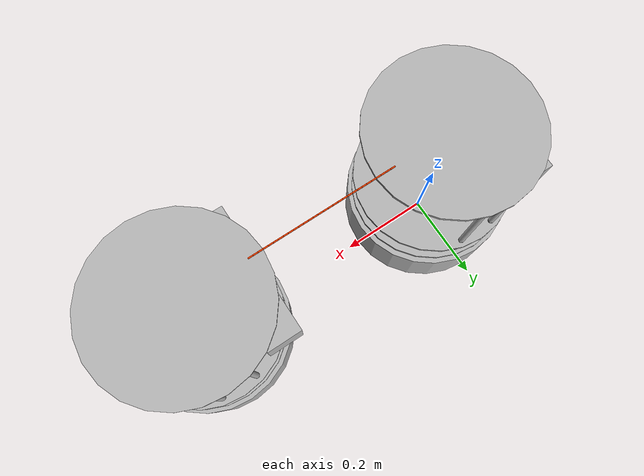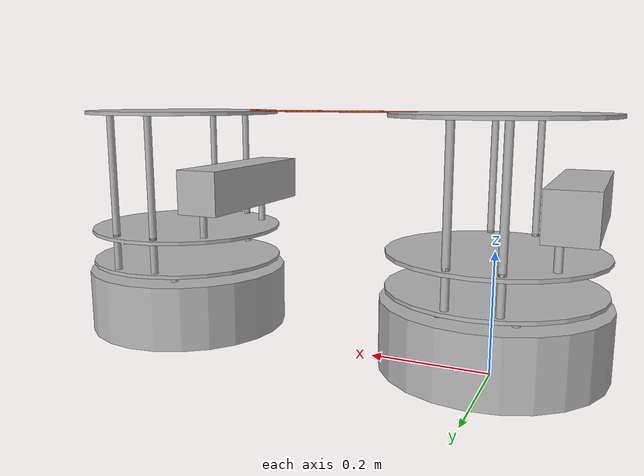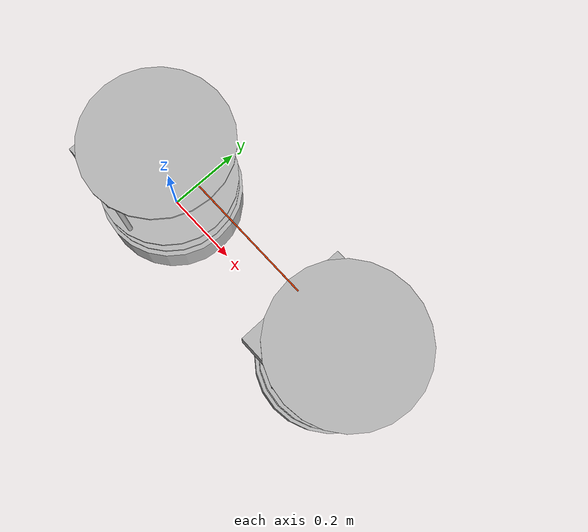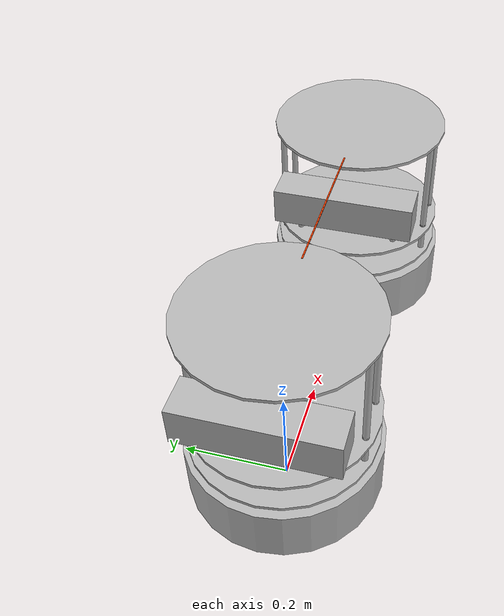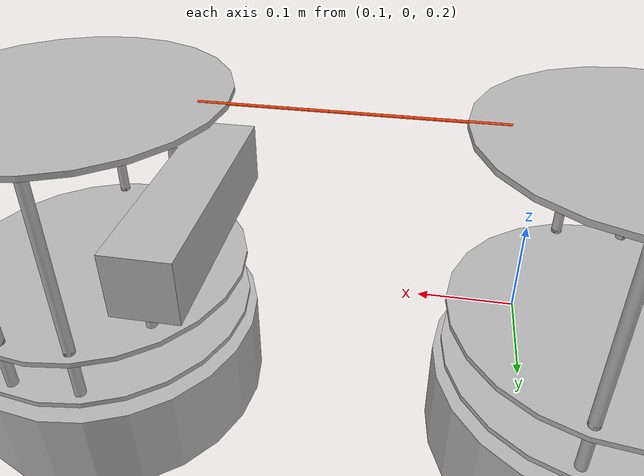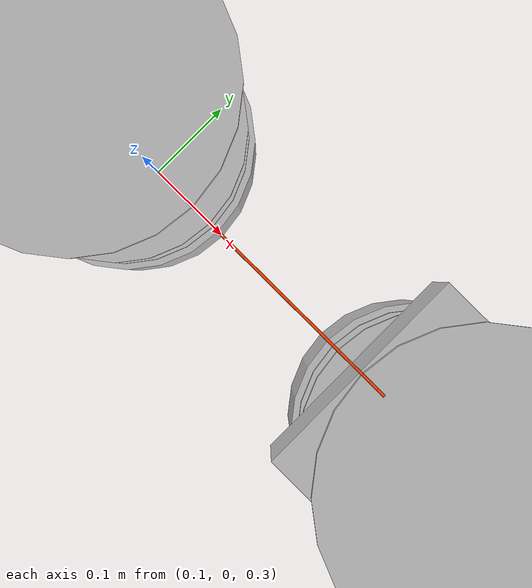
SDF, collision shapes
<?xml version="1.0" ?>
<sdf version="1.4">
  <model name="tethered_turtlebots">
<static>false</static>

  <!-- TURTLEBOT 1 -->
     <link name='base_foot1print'>
        <pose>0 0 0 0 -0 0</pose>
        <inertial>
          <pose>0.00947362 2.50779e-05 0.014919 0 -0 0</pose>
          <mass>2.4723</mass>
          <inertia>
            <ixx>0.0578436</ixx>
            <ixy>-2.91646e-06</ixy>
            <ixz>0.000317338</ixz>
            <iyy>0.0579316</iyy>
            <iyz>-9.59821e-07</iyz>
            <izz>0.0719963</izz>
          </inertia>
        </inertial>
        <collision name='base_foot1print_collision_base_link'>
          <pose>0 0 0.06969 0 -0 0</pose>
          <geometry>
            <cylinder>
              <length>0.10938</length>
              <radius>0.178</radius>
            </cylinder>
          </geometry>
          <surface>
            <contact>
              <ode/>
            </contact>
            <friction>
              <ode>
                <mu>0.3</mu>
                <mu2>0.3</mu2>
              </ode>
            </friction>
            <bounce/>
          </surface>
          <max_contacts>10</max_contacts>
        </collision>
        <collision name='base_foot1print_collision_camera_link'>
          <pose>-0.118 0 0.2812 0 -0 0</pose>
          <geometry>
            <box>
              <size>0.07271 0.27794 0.073</size>
            </box>
          </geometry>
          <surface>
            <contact>
              <ode/>
            </contact>
            <friction>
              <ode/>
            </friction>
            <bounce/>
          </surface>
          <max_contacts>10</max_contacts>
        </collision>
        <collision name='base_foot1print_collision_caster_back_link'>
          <pose>-0.135 0 0.0192 -1.5708 0 0</pose>
          <geometry>
            <cylinder>
              <length>0.0176</length>
              <radius>0.017</radius>
            </cylinder>
          </geometry>
          <surface>
            <contact>
              <ode>
                <kp>1e+06</kp>
                <kd>100</kd>
                <max_vel>1</max_vel>
                <min_depth>0.001</min_depth>
              </ode>
            </contact>
            <friction>
              <ode>
                <mu>0</mu>
                <mu2>0</mu2>
              </ode>
            </friction>
            <bounce/>
          </surface>
          <max_contacts>10</max_contacts>
        </collision>
        <collision name='base_foot1print_collision_caster_front_link'>
          <pose>0.115 0 0.0172 -1.5708 0 0</pose>
          <geometry>
            <cylinder>
              <length>0.0176</length>
              <radius>0.017</radius>
            </cylinder>
          </geometry>
          <surface>
            <contact>
              <ode>
                <kp>1e+06</kp>
                <kd>100</kd>
                <max_vel>1</max_vel>
                <min_depth>0.001</min_depth>
              </ode>
            </contact>
            <friction>
              <ode>
                <mu>0</mu>
                <mu2>0</mu2>
              </ode>
            </friction>
            <bounce/>
          </surface>
          <max_contacts>10</max_contacts>
        </collision>
        <collision name='base_foot1print_collision_plate_bottom_link'>
          <pose>0 0 0.1408 0 -0 0</pose>
          <geometry>
            <cylinder>
              <length>0.006</length>
              <radius>0.17</radius>
            </cylinder>
          </geometry>
          <max_contacts>10</max_contacts>
          <surface>
            <bounce/>
            <friction>
              <ode/>
            </friction>
            <contact>
              <ode/>
            </contact>
          </surface>
        </collision>
        <collision name='base_foot1print_collision_plate_middle_link'>
          <pose>0 0 0.1976 0 -0 0</pose>
          <geometry>
            <cylinder>
              <length>0.006</length>
              <radius>0.17</radius>
            </cylinder>
          </geometry>
          <max_contacts>10</max_contacts>
          <surface>
            <bounce/>
            <friction>
              <ode/>
            </friction>
            <contact>
              <ode/>
            </contact>
          </surface>
        </collision>
        <collision name='base_foot1print_collision_plate_top_link'>
          <pose>0 0 0.4068 0 -0 0</pose>
          <geometry>
            <cylinder>
              <length>0.006</length>
              <radius>0.17</radius>
            </cylinder>
          </geometry>
          <max_contacts>10</max_contacts>
          <surface>
            <bounce/>
            <friction>
              <ode/>
            </friction>
            <contact>
              <ode/>
            </contact>
          </surface>
        </collision>
        <collision name='base_foot1print_collision_pole_bottom_0_link'>
          <pose>0.12 0.082 0.113 0 -0 0</pose>
          <geometry>
            <cylinder>
              <length>0.0492</length>
              <radius>0.006</radius>
            </cylinder>
          </geometry>
          <max_contacts>10</max_contacts>
          <surface>
            <bounce/>
            <friction>
              <ode/>
            </friction>
            <contact>
              <ode/>
            </contact>
          </surface>
        </collision>
        <collision name='base_foot1print_collision_pole_bottom_1_link'>
          <pose>0.055 0.12 0.113 0 -0 0</pose>
          <geometry>
            <cylinder>
              <length>0.0492</length>
              <radius>0.006</radius>
            </cylinder>
          </geometry>
          <max_contacts>10</max_contacts>
          <surface>
            <bounce/>
            <friction>
              <ode/>
            </friction>
            <contact>
              <ode/>
            </contact>
          </surface>
        </collision>
        <collision name='base_foot1print_collision_pole_bottom_2_link'>
          <pose>-0.055 0.12 0.113 0 -0 0</pose>
          <geometry>
            <cylinder>
              <length>0.0492</length>
              <radius>0.006</radius>
            </cylinder>
          </geometry>
          <max_contacts>10</max_contacts>
          <surface>
            <bounce/>
            <friction>
              <ode/>
            </friction>
            <contact>
              <ode/>
            </contact>
          </surface>
        </collision>
        <collision name='base_foot1print_collision_pole_bottom_3_link'>
          <pose>0.12 -0.082 0.113 0 -0 0</pose>
          <geometry>
            <cylinder>
              <length>0.0492</length>
              <radius>0.006</radius>
            </cylinder>
          </geometry>
          <max_contacts>10</max_contacts>
          <surface>
            <bounce/>
            <friction>
              <ode/>
            </friction>
            <contact>
              <ode/>
            </contact>
          </surface>
        </collision>
        <collision name='base_foot1print_collision_pole_bottom_4_link'>
          <pose>0.055 -0.12 0.113 0 -0 0</pose>
          <geometry>
            <cylinder>
              <length>0.0492</length>
              <radius>0.006</radius>
            </cylinder>
          </geometry>
          <max_contacts>10</max_contacts>
          <surface>
            <bounce/>
            <friction>
              <ode/>
            </friction>
            <contact>
              <ode/>
            </contact>
          </surface>
        </collision>
        <collision name='base_foot1print_collision_pole_bottom_5_link'>
          <pose>-0.055 -0.12 0.113 0 -0 0</pose>
          <geometry>
            <cylinder>
              <length>0.0492</length>
              <radius>0.006</radius>
            </cylinder>
          </geometry>
          <max_contacts>10</max_contacts>
          <surface>
            <bounce/>
            <friction>
              <ode/>
            </friction>
            <contact>
              <ode/>
            </contact>
          </surface>
        </collision>
        <collision name='base_foot1print_collision_pole_kinect_0_link'>
          <pose>-0.1024 0.098 0.2474 0 -0 0</pose>
          <geometry>
            <cylinder>
              <length>0.0936</length>
              <radius>0.006</radius>
            </cylinder>
          </geometry>
          <max_contacts>10</max_contacts>
          <surface>
            <bounce/>
            <friction>
              <ode/>
            </friction>
            <contact>
              <ode/>
            </contact>
          </surface>
        </collision>
        <collision name='base_foot1print_collision_pole_kinect_1_link'>
          <pose>-0.1024 -0.098 0.2474 0 -0 0</pose>
          <geometry>
            <cylinder>
              <length>0.0936</length>
              <radius>0.006</radius>
            </cylinder>
          </geometry>
          <max_contacts>10</max_contacts>
          <surface>
            <bounce/>
            <friction>
              <ode/>
            </friction>
            <contact>
              <ode/>
            </contact>
          </surface>
        </collision>
        <collision name='base_foot1print_collision_pole_middle_0_link'>
          <pose>0.0381 0.1505 0.1742 0 -0 0</pose>
          <geometry>
            <cylinder>
              <length>0.0608</length>
              <radius>0.006</radius>
            </cylinder>
          </geometry>
          <max_contacts>10</max_contacts>
          <surface>
            <bounce/>
            <friction>
              <ode/>
            </friction>
            <contact>
              <ode/>
            </contact>
          </surface>
        </collision>
        <collision name='base_foot1print_collision_pole_middle_1_link'>
          <pose>0.0381 -0.1505 0.1742 0 -0 0</pose>
          <geometry>
            <cylinder>
              <length>0.0608</length>
              <radius>0.006</radius>
            </cylinder>
          </geometry>
          <max_contacts>10</max_contacts>
          <surface>
            <bounce/>
            <friction>
              <ode/>
            </friction>
            <contact>
              <ode/>
            </contact>
          </surface>
        </collision>
        <collision name='base_foot1print_collision_pole_middle_2_link'>
          <pose>-0.0381 0.1505 0.1742 0 -0 0</pose>
          <geometry>
            <cylinder>
              <length>0.0608</length>
              <radius>0.006</radius>
            </cylinder>
          </geometry>
          <max_contacts>10</max_contacts>
          <surface>
            <bounce/>
            <friction>
              <ode/>
            </friction>
            <contact>
              <ode/>
            </contact>
          </surface>
        </collision>
        <collision name='base_foot1print_collision_pole_middle_3_link'>
          <pose>-0.0381 -0.1505 0.1742 0 -0 0</pose>
          <geometry>
            <cylinder>
              <length>0.0608</length>
              <radius>0.006</radius>
            </cylinder>
          </geometry>
          <max_contacts>10</max_contacts>
          <surface>
            <bounce/>
            <friction>
              <ode/>
            </friction>
            <contact>
              <ode/>
            </contact>
          </surface>
        </collision>
        <collision name='base_foot1print_collision_pole_top_0_link'>
          <pose>0.0381 0.1505 0.3022 0 -0 0</pose>
          <geometry>
            <cylinder>
              <length>0.2032</length>
              <radius>0.006</radius>
            </cylinder>
          </geometry>
          <max_contacts>10</max_contacts>
          <surface>
            <bounce/>
            <friction>
              <ode/>
            </friction>
            <contact>
              <ode/>
            </contact>
          </surface>
        </collision>
        <collision name='base_foot1print_collision_pole_top_1_link'>
          <pose>0.0381 -0.1505 0.3022 0 -0 0</pose>
          <geometry>
            <cylinder>
              <length>0.2032</length>
              <radius>0.006</radius>
            </cylinder>
          </geometry>
          <max_contacts>10</max_contacts>
          <surface>
            <bounce/>
            <friction>
              <ode/>
            </friction>
            <contact>
              <ode/>
            </contact>
          </surface>
        </collision>
        <collision name='base_foot1print_collision_pole_top_2_link'>
          <pose>-0.0381 0.1505 0.3022 0 -0 0</pose>
          <geometry>
            <cylinder>
              <length>0.2032</length>
              <radius>0.006</radius>
            </cylinder>
          </geometry>
          <max_contacts>10</max_contacts>
          <surface>
            <bounce/>
            <friction>
              <ode/>
            </friction>
            <contact>
              <ode/>
            </contact>
          </surface>
        </collision>
        <collision name='base_foot1print_collision_pole_top_3_link'>
          <pose>-0.0381 -0.1505 0.3022 0 -0 0</pose>
          <geometry>
            <cylinder>
              <length>0.2032</length>
              <radius>0.006</radius>
            </cylinder>
          </geometry>
          <max_contacts>10</max_contacts>
          <surface>
            <bounce/>
            <friction>
              <ode/>
            </friction>
            <contact>
              <ode/>
            </contact>
          </surface>
        </collision>
        <visual name='base_foot1print_visual_base_link'>
          <pose>0.001 0 0.06219 0 -0 0</pose>
          <geometry>
            <mesh>
              <scale>1 1 1</scale>
              <uri>/opt/ros/indigo/share/kobuki_description/meshes/main_body.dae</uri>
            </mesh>
          </geometry>
        </visual>
        <visual name='base_foot1print_visual_camera_link'>
          <pose>-0.118 0 0.2812 0 -0 1.5708</pose>
          <geometry>
            <mesh>
              <scale>1 1 1</scale>
              <uri>/opt/ros/indigo/share/turtlebot_description/meshes/sensors/kinect.dae</uri>
            </mesh>
          </geometry>
        </visual>
        <visual name='base_foot1print_visual_plate_bottom_link'>
          <pose>0.02364 0 0.1408 0 -0 0</pose>
          <geometry>
            <mesh>
              <scale>1 1 1</scale>
              <uri>/opt/ros/indigo/share/turtlebot_description/meshes/stacks/hexagons/plate_bottom.dae</uri>
            </mesh>
          </geometry>
        </visual>
        <visual name='base_foot1print_visual_plate_middle_link'>
          <pose>-0.01364 0 0.1976 0 -0 0</pose>
          <geometry>
            <mesh>
              <scale>1 1 1</scale>
              <uri>/opt/ros/indigo/share/turtlebot_description/meshes/stacks/hexagons/plate_middle.dae</uri>
            </mesh>
          </geometry>
        </visual>
        <visual name='base_foot1print_visual_plate_top_link'>
          <pose>-0.01364 0 0.4068 0 -0 0</pose>
          <geometry>
            <mesh>
              <scale>1 1 1</scale>
              <uri>/opt/ros/indigo/share/turtlebot_description/meshes/stacks/hexagons/plate_top.dae</uri>
            </mesh>
          </geometry>
        </visual>
        <visual name='base_foot1print_visual_pole_bottom_0_link'>
          <pose>0.12 0.082 0.113 0 -0 0</pose>
          <geometry>
            <mesh>
              <scale>1 1 1</scale>
              <uri>/opt/ros/indigo/share/turtlebot_description/meshes/stacks/hexagons/pole_bottom.dae</uri>
            </mesh>
          </geometry>
        </visual>
        <visual name='base_foot1print_visual_pole_bottom_1_link'>
          <pose>0.055 0.12 0.113 0 -0 0</pose>
          <geometry>
            <mesh>
              <scale>1 1 1</scale>
              <uri>/opt/ros/indigo/share/turtlebot_description/meshes/stacks/hexagons/pole_bottom.dae</uri>
            </mesh>
          </geometry>
        </visual>
        <visual name='base_foot1print_visual_pole_bottom_2_link'>
          <pose>-0.055 0.12 0.113 0 -0 0</pose>
          <geometry>
            <mesh>
              <scale>1 1 1</scale>
              <uri>/opt/ros/indigo/share/turtlebot_description/meshes/stacks/hexagons/pole_bottom.dae</uri>
            </mesh>
          </geometry>
        </visual>
        <visual name='base_foot1print_visual_pole_bottom_3_link'>
          <pose>0.12 -0.082 0.113 0 -0 0</pose>
          <geometry>
            <mesh>
              <scale>1 1 1</scale>
              <uri>/opt/ros/indigo/share/turtlebot_description/meshes/stacks/hexagons/pole_bottom.dae</uri>
            </mesh>
          </geometry>
        </visual>
        <visual name='base_foot1print_visual_pole_bottom_4_link'>
          <pose>0.055 -0.12 0.113 0 -0 0</pose>
          <geometry>
            <mesh>
              <scale>1 1 1</scale>
              <uri>/opt/ros/indigo/share/turtlebot_description/meshes/stacks/hexagons/pole_bottom.dae</uri>
            </mesh>
          </geometry>
        </visual>
        <visual name='base_foot1print_visual_pole_bottom_5_link'>
          <pose>-0.055 -0.12 0.113 0 -0 0</pose>
          <geometry>
            <mesh>
              <scale>1 1 1</scale>
              <uri>/opt/ros/indigo/share/turtlebot_description/meshes/stacks/hexagons/pole_bottom.dae</uri>
            </mesh>
          </geometry>
        </visual>
        <visual name='base_foot1print_visual_pole_kinect_0_link'>
          <pose>-0.1024 0.098 0.2474 0 -0 0</pose>
          <geometry>
            <mesh>
              <scale>1 1 1</scale>
              <uri>/opt/ros/indigo/share/turtlebot_description/meshes/stacks/hexagons/pole_kinect.dae</uri>
            </mesh>
          </geometry>
        </visual>
        <visual name='base_foot1print_visual_pole_kinect_1_link'>
          <pose>-0.1024 -0.098 0.2474 0 -0 0</pose>
          <geometry>
            <mesh>
              <scale>1 1 1</scale>
              <uri>/opt/ros/indigo/share/turtlebot_description/meshes/stacks/hexagons/pole_kinect.dae</uri>
            </mesh>
          </geometry>
        </visual>
        <visual name='base_foot1print_visual_pole_middle_0_link'>
          <pose>0.0381 0.1505 0.1742 3.14159 -2.06823e-13 3.14159</pose>
          <geometry>
            <mesh>
              <scale>1 1 1</scale>
              <uri>/opt/ros/indigo/share/turtlebot_description/meshes/stacks/hexagons/pole_middle.dae</uri>
            </mesh>
          </geometry>
        </visual>
        <visual name='base_foot1print_visual_pole_middle_1_link'>
          <pose>0.0381 -0.1505 0.1742 3.14159 -2.06823e-13 3.14159</pose>
          <geometry>
            <mesh>
              <scale>1 1 1</scale>
              <uri>/opt/ros/indigo/share/turtlebot_description/meshes/stacks/hexagons/pole_middle.dae</uri>
            </mesh>
          </geometry>
        </visual>
        <visual name='base_foot1print_visual_pole_middle_2_link'>
          <pose>-0.0381 0.1505 0.1742 3.14159 -2.06823e-13 3.14159</pose>
          <geometry>
            <mesh>
              <scale>1 1 1</scale>
              <uri>/opt/ros/indigo/share/turtlebot_description/meshes/stacks/hexagons/pole_middle.dae</uri>
            </mesh>
          </geometry>
        </visual>
        <visual name='base_foot1print_visual_pole_middle_3_link'>
          <pose>-0.0381 -0.1505 0.1742 3.14159 -2.06823e-13 3.14159</pose>
          <geometry>
            <mesh>
              <scale>1 1 1</scale>
              <uri>/opt/ros/indigo/share/turtlebot_description/meshes/stacks/hexagons/pole_middle.dae</uri>
            </mesh>
          </geometry>
        </visual>
        <visual name='base_foot1print_visual_pole_top_0_link'>
          <pose>0.0381 0.1505 0.3022 0 -0 0</pose>
          <geometry>
            <mesh>
              <scale>1 1 1</scale>
              <uri>/opt/ros/indigo/share/turtlebot_description/meshes/stacks/hexagons/pole_top.dae</uri>
            </mesh>
          </geometry>
        </visual>
        <visual name='base_foot1print_visual_pole_top_1_link'>
          <pose>0.0381 -0.1505 0.3022 0 -0 0</pose>
          <geometry>
            <mesh>
              <scale>1 1 1</scale>
              <uri>/opt/ros/indigo/share/turtlebot_description/meshes/stacks/hexagons/pole_top.dae</uri>
            </mesh>
          </geometry>
        </visual>
        <visual name='base_foot1print_visual_pole_top_2_link'>
          <pose>-0.0381 0.1505 0.3022 0 -0 0</pose>
          <geometry>
            <mesh>
              <scale>1 1 1</scale>
              <uri>/opt/ros/indigo/share/turtlebot_description/meshes/stacks/hexagons/pole_top.dae</uri>
            </mesh>
          </geometry>
        </visual>
        <visual name='base_foot1print_visual_pole_top_3_link'>
          <pose>-0.0381 -0.1505 0.3022 0 -0 0</pose>
          <geometry>
            <mesh>
              <scale>1 1 1</scale>
              <uri>/opt/ros/indigo/share/turtlebot_description/meshes/stacks/hexagons/pole_top.dae</uri>
            </mesh>
          </geometry>
        </visual>
        <velocity_decay>
          <linear>0</linear>
          <angular>0</angular>
        </velocity_decay>
        <sensor name='bumpers' type='contact'>
          <always_on>1</always_on>
          <update_rate>50</update_rate>
          <visualize>1</visualize>
          <contact>
            <collision>base_foot1print_collision_base_link</collision>
            <topic>__default_topic__</topic>
          </contact>
          <pose>0 0 0.0102 0 -0 0</pose>
        </sensor>
        <velocity_decay>
          <linear>0</linear>
          <angular>0</angular>
        </velocity_decay>
        <sensor name='camera' type='depth'>
          <always_on>1</always_on>
          <update_rate>20</update_rate>
          <camera name='__default__'>
            <horizontal_fov>1.0472</horizontal_fov>
            <image>
              <format>R8G8B8</format>
              <width>640</width>
              <height>480</height>
            </image>
            <clip>
              <near>0.05</near>
              <far>8</far>
            </clip>
          </camera>
          <plugin name='kinect_camera_controller' filename='libgazebo_ros_openni_kinect.so'>
            <cameraName>camera</cameraName>
            <alwaysOn>true</alwaysOn>
            <updateRate>10</updateRate>
            <imageTopicName>rgb/image_raw</imageTopicName>
            <depthImageTopicName>depth/image_raw</depthImageTopicName>
            <pointCloudTopicName>depth/points</pointCloudTopicName>
            <cameraInfoTopicName>rgb/camera_info</cameraInfoTopicName>
            <depthImageCameraInfoTopicName>depth/camera_info</depthImageCameraInfoTopicName>
            <frameName>camera_depth_optical_frame</frameName>
            <baseline>0.1</baseline>
            <distortion_k1>0.0</distortion_k1>
            <distortion_k2>0.0</distortion_k2>
            <distortion_k3>0.0</distortion_k3>
            <distortion_t1>0.0</distortion_t1>
            <distortion_t2>0.0</distortion_t2>
            <pointCloudCutoff>0.4</pointCloudCutoff>
            <robotNamespace>/turtle1</robotNamespace>
          </plugin>
          <pose>-0.118 0 0.2812 0 -0 0</pose>
        </sensor>
        <velocity_decay>
          <linear>0</linear>
          <angular>0</angular>
        </velocity_decay>
        <velocity_decay>
          <linear>0</linear>
          <angular>0</angular>
        </velocity_decay>
        <velocity_decay>
          <linear>0</linear>
          <angular>0</angular>
        </velocity_decay>
        <sensor name='cliff_sensor_front' type='ray'>
          <always_on>1</always_on>
          <update_rate>50</update_rate>
          <visualize>1</visualize>
          <ray>
            <scan>
              <horizontal>
                <samples>50</samples>
                <resolution>1</resolution>
                <min_angle>-0.0436</min_angle>
                <max_angle>0.0436</max_angle>
              </horizontal>
            </scan>
            <range>
              <min>0.01</min>
              <max>0.15</max>
              <resolution>1</resolution>
            </range>
          </ray>
          <pose>0.156 0 0.0316 3.14159 1.57079 3.14159</pose>
        </sensor>
        <velocity_decay>
          <linear>0</linear>
          <angular>0</angular>
        </velocity_decay>
        <sensor name='cliff_sensor_left' type='ray'>
          <always_on>1</always_on>
          <update_rate>50</update_rate>
          <visualize>1</visualize>
          <ray>
            <scan>
              <horizontal>
                <samples>50</samples>
                <resolution>1</resolution>
                <min_angle>-0.0436</min_angle>
                <max_angle>0.0436</max_angle>
              </horizontal>
            </scan>
            <range>
              <min>0.01</min>
              <max>0.15</max>
              <resolution>1</resolution>
            </range>
          </ray>
          <pose>0.08734 0.13601 0.0316 3.14159 1.57079 3.14159</pose>
        </sensor>
        <velocity_decay>
          <linear>0</linear>
          <angular>0</angular>
        </velocity_decay>
        <sensor name='cliff_sensor_right' type='ray'>
          <always_on>1</always_on>
          <update_rate>50</update_rate>
          <visualize>1</visualize>
          <ray>
            <scan>
              <horizontal>
                <samples>50</samples>
                <resolution>1</resolution>
                <min_angle>-0.0436</min_angle>
                <max_angle>0.0436</max_angle>
              </horizontal>
            </scan>
            <range>
              <min>0.01</min>
              <max>0.15</max>
              <resolution>1</resolution>
            </range>
          </ray>
          <pose>0.085 -0.13601 0.0316 3.14159 1.57079 3.14159</pose>
        </sensor>
        <gravity>1</gravity>
        <velocity_decay>
          <linear>0</linear>
          <angular>0</angular>
        </velocity_decay>
        <self_collide>0</self_collide>
        <sensor name='imu' type='imu'>
          <always_on>1</always_on>
          <update_rate>50</update_rate>
          <visualize>0</visualize>
          <imu>
            <noise>
              <type>gaussian</type>
              <rate>
                <mean>0</mean>
                <stddev>1.96e-06</stddev>
                <bias_mean>0</bias_mean>
                <bias_stddev>0</bias_stddev>
              </rate>
              <accel>
                <mean>0</mean>
                <stddev>0.017</stddev>
                <bias_mean>0.1</bias_mean>
                <bias_stddev>0.001</bias_stddev>
              </accel>
            </noise>
          </imu>
          <pose>0.056 0.062 0.0304 0 -0 0</pose>
        </sensor>
        <kinematic>0</kinematic>
      </link>
      <link name='wheel1_left_link'>
        <pose>0 0.115 0.0352 -1.5708 0 0</pose>
        <inertial>
          <pose>0 0 0 0 -0 0</pose>
          <mass>0.01</mass>
          <inertia>
            <ixx>0.001</ixx>
            <ixy>0</ixy>
            <ixz>0</ixz>
            <iyy>0.001</iyy>
            <iyz>0</iyz>
            <izz>0.001</izz>
          </inertia>
        </inertial>
        <collision name='wheel1_left_link_collision'>
          <pose>0 0 0 0 -0 0</pose>
          <geometry>
            <cylinder>
              <length>0.0206</length>
              <radius>0.0352</radius>
            </cylinder>
          </geometry>
          <surface>
            <contact>
              <ode>
                <kp>1e+06</kp>
                <kd>100</kd>
                <max_vel>1</max_vel>
                <min_depth>0.001</min_depth>
              </ode>
            </contact>
            <friction>
              <ode>
                <mu>1</mu>
                <mu2>1</mu2>
              </ode>
            </friction>
            <bounce/>
          </surface>
          <max_contacts>10</max_contacts>
        </collision>
        <visual name='wheel1_left_link_visual'>
          <pose>0 0 0 0 -0 0</pose>
          <geometry>
            <mesh>
              <scale>1 1 1</scale>
              <uri>/opt/ros/indigo/share/kobuki_description/meshes/wheel.dae</uri>
            </mesh>
          </geometry>
        </visual>
        <gravity>1</gravity>
        <velocity_decay>
          <linear>0</linear>
          <angular>0</angular>
        </velocity_decay>
        <self_collide>0</self_collide>
        <kinematic>0</kinematic>
      </link>
      <joint name='wheel1_left_joint' type='revolute'>
        <child>wheel1_left_link</child>
        <parent>base_foot1print</parent>
        <axis>
          <xyz>0 1 0</xyz>
          <limit>
            <lower>-1e+16</lower>
            <upper>1e+16</upper>
          </limit>
          <dynamics/>
        </axis>
      </joint>
      <link name='wheel1_right_link'>
        <pose>0 -0.115 0.0352 -1.5708 0 0</pose>
        <inertial>
          <pose>0 0 0 0 -0 0</pose>
          <mass>0.01</mass>
          <inertia>
            <ixx>0.001</ixx>
            <ixy>0</ixy>
            <ixz>0</ixz>
            <iyy>0.001</iyy>
            <iyz>0</iyz>
            <izz>0.001</izz>
          </inertia>
        </inertial>
        <collision name='wheel1_right_link_collision'>
          <pose>0 0 0 0 -0 0</pose>
          <geometry>
            <cylinder>
              <length>0.0206</length>
              <radius>0.035</radius>
            </cylinder>
          </geometry>
          <surface>
            <contact>
              <ode>
                <kp>1e+06</kp>
                <kd>100</kd>
                <max_vel>1</max_vel>
                <min_depth>0.001</min_depth>
              </ode>
            </contact>
            <friction>
              <ode>
                <mu>1</mu>
                <mu2>1</mu2>
              </ode>
            </friction>
            <bounce/>
          </surface>
          <max_contacts>10</max_contacts>
        </collision>
        <visual name='wheel1_right_link_visual'>
          <pose>0 0 0 0 -0 0</pose>
          <geometry>
            <mesh>
              <scale>1 1 1</scale>
              <uri>/opt/ros/indigo/share/kobuki_description/meshes/wheel.dae</uri>
            </mesh>
          </geometry>
        </visual>
        <gravity>1</gravity>
        <velocity_decay>
          <linear>0</linear>
          <angular>0</angular>
        </velocity_decay>
        <self_collide>0</self_collide>
        <kinematic>0</kinematic>
      </link>
      <joint name='wheel1_right_joint' type='revolute'>
        <child>wheel1_right_link</child>
        <parent>base_foot1print</parent>
        <axis>
          <xyz>0 1 0</xyz>
          <limit>
            <lower>-1e+16</lower>
            <upper>1e+16</upper>
          </limit>
          <dynamics/>
        </axis>
      </joint>
      <static>0</static>
      <plugin name='kobuki_controller' filename='libgazebo_ros_diff_drive.so'>
        <publish_tf>1</publish_tf>
        <leftJoint>wheel1_left_joint</leftJoint>
        <rightJoint>wheel1_right_joint</rightJoint>
        <wheelSeparation>.230</wheelSeparation>
        <wheelDiameter>0.070</wheelDiameter>
        <wheelTorque>1.0</wheelTorque>
        <velocity_command_timeout>0.6</velocity_command_timeout>
        <cliff_sensor_left_name>cliff_sensor_left</cliff_sensor_left_name>
        <cliff_sensor_center_name>cliff_sensor_front</cliff_sensor_center_name>
        <cliff_sensor_right_name>cliff_sensor_right</cliff_sensor_right_name>
        <cliff_detection_threshold>0.04</cliff_detection_threshold>
        <bumper_name>bumpers</bumper_name>
        <imu_name>imu</imu_name>
        <robotNamespace>/turtle1</robotNamespace>
      </plugin>

	  <!-- TURTLEBOT 2 -->
     <link name='base_foot2print'>
        <pose>0.57 0 0 0 -0 0</pose>
        <inertial>
          <pose>0.00947362 2.50779e-05 0.014919 0 -0 0</pose>
          <mass>2.4723</mass>
          <inertia>
            <ixx>0.0578436</ixx>
            <ixy>-2.91646e-06</ixy>
            <ixz>0.000317338</ixz>
            <iyy>0.0579316</iyy>
            <iyz>-9.59821e-07</iyz>
            <izz>0.0719963</izz>
          </inertia>
        </inertial>
        <collision name='base_foot2print_collision_base_link'>
          <pose>0 0 0.06969 0 -0 0</pose>
          <geometry>
            <cylinder>
              <length>0.10938</length>
              <radius>0.178</radius>
            </cylinder>
          </geometry>
          <surface>
            <contact>
              <ode/>
            </contact>
            <friction>
              <ode>
                <mu>0.3</mu>
                <mu2>0.3</mu2>
              </ode>
            </friction>
            <bounce/>
          </surface>
          <max_contacts>10</max_contacts>
        </collision>
        <collision name='base_foot2print_collision_camera_link'>
          <pose>-0.118 0 0.2812 0 -0 0</pose>
          <geometry>
            <box>
              <size>0.07271 0.27794 0.073</size>
            </box>
          </geometry>
          <surface>
            <contact>
              <ode/>
            </contact>
            <friction>
              <ode/>
            </friction>
            <bounce/>
          </surface>
          <max_contacts>10</max_contacts>
        </collision>
        <collision name='base_foot2print_collision_caster_back_link'>
          <pose>-0.135 0 0.0192 -1.5708 0 0</pose>
          <geometry>
            <cylinder>
              <length>0.0176</length>
              <radius>0.017</radius>
            </cylinder>
          </geometry>
          <surface>
            <contact>
              <ode>
                <kp>1e+06</kp>
                <kd>100</kd>
                <max_vel>1</max_vel>
                <min_depth>0.001</min_depth>
              </ode>
            </contact>
            <friction>
              <ode>
                <mu>0</mu>
                <mu2>0</mu2>
              </ode>
            </friction>
            <bounce/>
          </surface>
          <max_contacts>10</max_contacts>
        </collision>
        <collision name='base_foot2print_collision_caster_front_link'>
          <pose>0.115 0 0.0172 -1.5708 0 0</pose>
          <geometry>
            <cylinder>
              <length>0.0176</length>
              <radius>0.017</radius>
            </cylinder>
          </geometry>
          <surface>
            <contact>
              <ode>
                <kp>1e+06</kp>
                <kd>100</kd>
                <max_vel>1</max_vel>
                <min_depth>0.001</min_depth>
              </ode>
            </contact>
            <friction>
              <ode>
                <mu>0</mu>
                <mu2>0</mu2>
              </ode>
            </friction>
            <bounce/>
          </surface>
          <max_contacts>10</max_contacts>
        </collision>
        <collision name='base_foot2print_collision_plate_bottom_link'>
          <pose>0 0 0.1408 0 -0 0</pose>
          <geometry>
            <cylinder>
              <length>0.006</length>
              <radius>0.17</radius>
            </cylinder>
          </geometry>
          <max_contacts>10</max_contacts>
          <surface>
            <bounce/>
            <friction>
              <ode/>
            </friction>
            <contact>
              <ode/>
            </contact>
          </surface>
        </collision>
        <collision name='base_foot2print_collision_plate_middle_link'>
          <pose>0 0 0.1976 0 -0 0</pose>
          <geometry>
            <cylinder>
              <length>0.006</length>
              <radius>0.17</radius>
            </cylinder>
          </geometry>
          <max_contacts>10</max_contacts>
          <surface>
            <bounce/>
            <friction>
              <ode/>
            </friction>
            <contact>
              <ode/>
            </contact>
          </surface>
        </collision>
        <collision name='base_foot2print_collision_plate_top_link'>
          <pose>0 0 0.4068 0 -0 0</pose>
          <geometry>
            <cylinder>
              <length>0.006</length>
              <radius>0.17</radius>
            </cylinder>
          </geometry>
          <max_contacts>10</max_contacts>
          <surface>
            <bounce/>
            <friction>
              <ode/>
            </friction>
            <contact>
              <ode/>
            </contact>
          </surface>
        </collision>
        <collision name='base_foot2print_collision_pole_bottom_0_link'>
          <pose>0.12 0.082 0.113 0 -0 0</pose>
          <geometry>
            <cylinder>
              <length>0.0492</length>
              <radius>0.006</radius>
            </cylinder>
          </geometry>
          <max_contacts>10</max_contacts>
          <surface>
            <bounce/>
            <friction>
              <ode/>
            </friction>
            <contact>
              <ode/>
            </contact>
          </surface>
        </collision>
        <collision name='base_foot2print_collision_pole_bottom_1_link'>
          <pose>0.055 0.12 0.113 0 -0 0</pose>
          <geometry>
            <cylinder>
              <length>0.0492</length>
              <radius>0.006</radius>
            </cylinder>
          </geometry>
          <max_contacts>10</max_contacts>
          <surface>
            <bounce/>
            <friction>
              <ode/>
            </friction>
            <contact>
              <ode/>
            </contact>
          </surface>
        </collision>
        <collision name='base_foot2print_collision_pole_bottom_2_link'>
          <pose>-0.055 0.12 0.113 0 -0 0</pose>
          <geometry>
            <cylinder>
              <length>0.0492</length>
              <radius>0.006</radius>
            </cylinder>
          </geometry>
          <max_contacts>10</max_contacts>
          <surface>
            <bounce/>
            <friction>
              <ode/>
            </friction>
            <contact>
              <ode/>
            </contact>
          </surface>
        </collision>
        <collision name='base_foot2print_collision_pole_bottom_3_link'>
          <pose>0.12 -0.082 0.113 0 -0 0</pose>
          <geometry>
            <cylinder>
              <length>0.0492</length>
              <radius>0.006</radius>
            </cylinder>
          </geometry>
          <max_contacts>10</max_contacts>
          <surface>
            <bounce/>
            <friction>
              <ode/>
            </friction>
            <contact>
              <ode/>
            </contact>
          </surface>
        </collision>
        <collision name='base_foot2print_collision_pole_bottom_4_link'>
          <pose>0.055 -0.12 0.113 0 -0 0</pose>
          <geometry>
            <cylinder>
              <length>0.0492</length>
              <radius>0.006</radius>
            </cylinder>
          </geometry>
          <max_contacts>10</max_contacts>
          <surface>
            <bounce/>
            <friction>
              <ode/>
            </friction>
            <contact>
              <ode/>
            </contact>
          </surface>
        </collision>
        <collision name='base_foot2print_collision_pole_bottom_5_link'>
          <pose>-0.055 -0.12 0.113 0 -0 0</pose>
          <geometry>
            <cylinder>
              <length>0.0492</length>
              <radius>0.006</radius>
            </cylinder>
          </geometry>
          <max_contacts>10</max_contacts>
          <surface>
            <bounce/>
            <friction>
              <ode/>
            </friction>
            <contact>
              <ode/>
            </contact>
          </surface>
        </collision>
        <collision name='base_foot2print_collision_pole_kinect_0_link'>
          <pose>-0.1024 0.098 0.2474 0 -0 0</pose>
          <geometry>
            <cylinder>
              <length>0.0936</length>
              <radius>0.006</radius>
            </cylinder>
          </geometry>
          <max_contacts>10</max_contacts>
          <surface>
            <bounce/>
            <friction>
              <ode/>
            </friction>
            <contact>
              <ode/>
            </contact>
          </surface>
        </collision>
        <collision name='base_foot2print_collision_pole_kinect_1_link'>
          <pose>-0.1024 -0.098 0.2474 0 -0 0</pose>
          <geometry>
            <cylinder>
              <length>0.0936</length>
              <radius>0.006</radius>
            </cylinder>
          </geometry>
          <max_contacts>10</max_contacts>
          <surface>
            <bounce/>
            <friction>
              <ode/>
            </friction>
            <contact>
              <ode/>
            </contact>
          </surface>
        </collision>
        <collision name='base_foot2print_collision_pole_middle_0_link'>
          <pose>0.0381 0.1505 0.1742 0 -0 0</pose>
          <geometry>
            <cylinder>
              <length>0.0608</length>
              <radius>0.006</radius>
            </cylinder>
          </geometry>
          <max_contacts>10</max_contacts>
          <surface>
            <bounce/>
            <friction>
              <ode/>
            </friction>
            <contact>
              <ode/>
            </contact>
          </surface>
        </collision>
        <collision name='base_foot2print_collision_pole_middle_1_link'>
          <pose>0.0381 -0.1505 0.1742 0 -0 0</pose>
          <geometry>
            <cylinder>
              <length>0.0608</length>
              <radius>0.006</radius>
            </cylinder>
          </geometry>
          <max_contacts>10</max_contacts>
          <surface>
            <bounce/>
            <friction>
              <ode/>
            </friction>
            <contact>
              <ode/>
            </contact>
          </surface>
        </collision>
        <collision name='base_foot2print_collision_pole_middle_2_link'>
          <pose>-0.0381 0.1505 0.1742 0 -0 0</pose>
          <geometry>
            <cylinder>
              <length>0.0608</length>
              <radius>0.006</radius>
            </cylinder>
          </geometry>
          <max_contacts>10</max_contacts>
          <surface>
            <bounce/>
            <friction>
              <ode/>
            </friction>
            <contact>
              <ode/>
            </contact>
          </surface>
        </collision>
        <collision name='base_foot2print_collision_pole_middle_3_link'>
          <pose>-0.0381 -0.1505 0.1742 0 -0 0</pose>
          <geometry>
            <cylinder>
              <length>0.0608</length>
              <radius>0.006</radius>
            </cylinder>
          </geometry>
          <max_contacts>10</max_contacts>
          <surface>
            <bounce/>
            <friction>
              <ode/>
            </friction>
            <contact>
              <ode/>
            </contact>
          </surface>
        </collision>
        <collision name='base_foot2print_collision_pole_top_0_link'>
          <pose>0.0381 0.1505 0.3022 0 -0 0</pose>
          <geometry>
            <cylinder>
              <length>0.2032</length>
              <radius>0.006</radius>
            </cylinder>
          </geometry>
          <max_contacts>10</max_contacts>
          <surface>
            <bounce/>
            <friction>
              <ode/>
            </friction>
            <contact>
              <ode/>
            </contact>
          </surface>
        </collision>
        <collision name='base_foot2print_collision_pole_top_1_link'>
          <pose>0.0381 -0.1505 0.3022 0 -0 0</pose>
          <geometry>
            <cylinder>
              <length>0.2032</length>
              <radius>0.006</radius>
            </cylinder>
          </geometry>
          <max_contacts>10</max_contacts>
          <surface>
            <bounce/>
            <friction>
              <ode/>
            </friction>
            <contact>
              <ode/>
            </contact>
          </surface>
        </collision>
        <collision name='base_foot2print_collision_pole_top_2_link'>
          <pose>-0.0381 0.1505 0.3022 0 -0 0</pose>
          <geometry>
            <cylinder>
              <length>0.2032</length>
              <radius>0.006</radius>
            </cylinder>
          </geometry>
          <max_contacts>10</max_contacts>
          <surface>
            <bounce/>
            <friction>
              <ode/>
            </friction>
            <contact>
              <ode/>
            </contact>
          </surface>
        </collision>
        <collision name='base_foot2print_collision_pole_top_3_link'>
          <pose>-0.0381 -0.1505 0.3022 0 -0 0</pose>
          <geometry>
            <cylinder>
              <length>0.2032</length>
              <radius>0.006</radius>
            </cylinder>
          </geometry>
          <max_contacts>10</max_contacts>
          <surface>
            <bounce/>
            <friction>
              <ode/>
            </friction>
            <contact>
              <ode/>
            </contact>
          </surface>
        </collision>
        <visual name='base_foot2print_visual_base_link'>
          <pose>0.001 0 0.06219 0 -0 0</pose>
          <geometry>
            <mesh>
              <scale>1 1 1</scale>
              <uri>/opt/ros/indigo/share/kobuki_description/meshes/main_body.dae</uri>
            </mesh>
          </geometry>
        </visual>
        <visual name='base_foot2print_visual_camera_link'>
          <pose>-0.118 0 0.2812 0 -0 1.5708</pose>
          <geometry>
            <mesh>
              <scale>1 1 1</scale>
              <uri>/opt/ros/indigo/share/turtlebot_description/meshes/sensors/kinect.dae</uri>
            </mesh>
          </geometry>
        </visual>
        <visual name='base_foot2print_visual_plate_bottom_link'>
          <pose>0.02364 0 0.1408 0 -0 0</pose>
          <geometry>
            <mesh>
              <scale>1 1 1</scale>
              <uri>/opt/ros/indigo/share/turtlebot_description/meshes/stacks/hexagons/plate_bottom.dae</uri>
            </mesh>
          </geometry>
        </visual>
        <visual name='base_foot2print_visual_plate_middle_link'>
          <pose>-0.01364 0 0.1976 0 -0 0</pose>
          <geometry>
            <mesh>
              <scale>1 1 1</scale>
              <uri>/opt/ros/indigo/share/turtlebot_description/meshes/stacks/hexagons/plate_middle.dae</uri>
            </mesh>
          </geometry>
        </visual>
        <visual name='base_foot2print_visual_plate_top_link'>
          <pose>-0.01364 0 0.4068 0 -0 0</pose>
          <geometry>
            <mesh>
              <scale>1 1 1</scale>
              <uri>/opt/ros/indigo/share/turtlebot_description/meshes/stacks/hexagons/plate_top.dae</uri>
            </mesh>
          </geometry>
        </visual>
        <visual name='base_foot2print_visual_pole_bottom_0_link'>
          <pose>0.12 0.082 0.113 0 -0 0</pose>
          <geometry>
            <mesh>
              <scale>1 1 1</scale>
              <uri>/opt/ros/indigo/share/turtlebot_description/meshes/stacks/hexagons/pole_bottom.dae</uri>
            </mesh>
          </geometry>
        </visual>
        <visual name='base_foot2print_visual_pole_bottom_1_link'>
          <pose>0.055 0.12 0.113 0 -0 0</pose>
          <geometry>
            <mesh>
              <scale>1 1 1</scale>
              <uri>/opt/ros/indigo/share/turtlebot_description/meshes/stacks/hexagons/pole_bottom.dae</uri>
            </mesh>
          </geometry>
        </visual>
        <visual name='base_foot2print_visual_pole_bottom_2_link'>
          <pose>-0.055 0.12 0.113 0 -0 0</pose>
          <geometry>
            <mesh>
              <scale>1 1 1</scale>
              <uri>/opt/ros/indigo/share/turtlebot_description/meshes/stacks/hexagons/pole_bottom.dae</uri>
            </mesh>
          </geometry>
        </visual>
        <visual name='base_foot2print_visual_pole_bottom_3_link'>
          <pose>0.12 -0.082 0.113 0 -0 0</pose>
          <geometry>
            <mesh>
              <scale>1 1 1</scale>
              <uri>/opt/ros/indigo/share/turtlebot_description/meshes/stacks/hexagons/pole_bottom.dae</uri>
            </mesh>
          </geometry>
        </visual>
        <visual name='base_foot2print_visual_pole_bottom_4_link'>
          <pose>0.055 -0.12 0.113 0 -0 0</pose>
          <geometry>
            <mesh>
              <scale>1 1 1</scale>
              <uri>/opt/ros/indigo/share/turtlebot_description/meshes/stacks/hexagons/pole_bottom.dae</uri>
            </mesh>
          </geometry>
        </visual>
        <visual name='base_foot2print_visual_pole_bottom_5_link'>
          <pose>-0.055 -0.12 0.113 0 -0 0</pose>
          <geometry>
            <mesh>
              <scale>1 1 1</scale>
              <uri>/opt/ros/indigo/share/turtlebot_description/meshes/stacks/hexagons/pole_bottom.dae</uri>
            </mesh>
          </geometry>
        </visual>
        <visual name='base_foot2print_visual_pole_kinect_0_link'>
          <pose>-0.1024 0.098 0.2474 0 -0 0</pose>
          <geometry>
            <mesh>
              <scale>1 1 1</scale>
              <uri>/opt/ros/indigo/share/turtlebot_description/meshes/stacks/hexagons/pole_kinect.dae</uri>
            </mesh>
          </geometry>
        </visual>
        <visual name='base_foot2print_visual_pole_kinect_1_link'>
          <pose>-0.1024 -0.098 0.2474 0 -0 0</pose>
          <geometry>
            <mesh>
              <scale>1 1 1</scale>
              <uri>/opt/ros/indigo/share/turtlebot_description/meshes/stacks/hexagons/pole_kinect.dae</uri>
            </mesh>
          </geometry>
        </visual>
        <visual name='base_foot2print_visual_pole_middle_0_link'>
          <pose>0.0381 0.1505 0.1742 3.14159 -2.06823e-13 3.14159</pose>
          <geometry>
            <mesh>
              <scale>1 1 1</scale>
              <uri>/opt/ros/indigo/share/turtlebot_description/meshes/stacks/hexagons/pole_middle.dae</uri>
            </mesh>
          </geometry>
        </visual>
        <visual name='base_foot2print_visual_pole_middle_1_link'>
          <pose>0.0381 -0.1505 0.1742 3.14159 -2.06823e-13 3.14159</pose>
          <geometry>
            <mesh>
              <scale>1 1 1</scale>
              <uri>/opt/ros/indigo/share/turtlebot_description/meshes/stacks/hexagons/pole_middle.dae</uri>
            </mesh>
          </geometry>
        </visual>
        <visual name='base_foot2print_visual_pole_middle_2_link'>
          <pose>-0.0381 0.1505 0.1742 3.14159 -2.06823e-13 3.14159</pose>
          <geometry>
            <mesh>
              <scale>1 1 1</scale>
              <uri>/opt/ros/indigo/share/turtlebot_description/meshes/stacks/hexagons/pole_middle.dae</uri>
            </mesh>
          </geometry>
        </visual>
        <visual name='base_foot2print_visual_pole_middle_3_link'>
          <pose>-0.0381 -0.1505 0.1742 3.14159 -2.06823e-13 3.14159</pose>
          <geometry>
            <mesh>
              <scale>1 1 1</scale>
              <uri>/opt/ros/indigo/share/turtlebot_description/meshes/stacks/hexagons/pole_middle.dae</uri>
            </mesh>
          </geometry>
        </visual>
        <visual name='base_foot2print_visual_pole_top_0_link'>
          <pose>0.0381 0.1505 0.3022 0 -0 0</pose>
          <geometry>
            <mesh>
              <scale>1 1 1</scale>
              <uri>/opt/ros/indigo/share/turtlebot_description/meshes/stacks/hexagons/pole_top.dae</uri>
            </mesh>
          </geometry>
        </visual>
        <visual name='base_foot2print_visual_pole_top_1_link'>
          <pose>0.0381 -0.1505 0.3022 0 -0 0</pose>
          <geometry>
            <mesh>
              <scale>1 1 1</scale>
              <uri>/opt/ros/indigo/share/turtlebot_description/meshes/stacks/hexagons/pole_top.dae</uri>
            </mesh>
          </geometry>
        </visual>
        <visual name='base_foot2print_visual_pole_top_2_link'>
          <pose>-0.0381 0.1505 0.3022 0 -0 0</pose>
          <geometry>
            <mesh>
              <scale>1 1 1</scale>
              <uri>/opt/ros/indigo/share/turtlebot_description/meshes/stacks/hexagons/pole_top.dae</uri>
            </mesh>
          </geometry>
        </visual>
        <visual name='base_foot2print_visual_pole_top_3_link'>
          <pose>-0.0381 -0.1505 0.3022 0 -0 0</pose>
          <geometry>
            <mesh>
              <scale>1 1 1</scale>
              <uri>/opt/ros/indigo/share/turtlebot_description/meshes/stacks/hexagons/pole_top.dae</uri>
            </mesh>
          </geometry>
        </visual>
        <velocity_decay>
          <linear>0</linear>
          <angular>0</angular>
        </velocity_decay>
        <sensor name='bumpers' type='contact'>
          <always_on>1</always_on>
          <update_rate>50</update_rate>
          <visualize>1</visualize>
          <contact>
            <collision>base_foot2print_collision_base_link</collision>
            <topic>__default_topic__</topic>
          </contact>
          <pose>0 0 0.0102 0 -0 0</pose>
        </sensor>
        <velocity_decay>
          <linear>0</linear>
          <angular>0</angular>
        </velocity_decay>
        <sensor name='camera' type='depth'>
          <always_on>1</always_on>
          <update_rate>20</update_rate>
          <camera name='__default__'>
            <horizontal_fov>1.0472</horizontal_fov>
            <image>
              <format>R8G8B8</format>
              <width>640</width>
              <height>480</height>
            </image>
            <clip>
              <near>0.05</near>
              <far>8</far>
            </clip>
          </camera>
          <plugin name='kinect_camera_controller' filename='libgazebo_ros_openni_kinect.so'>
            <cameraName>camera</cameraName>
            <alwaysOn>true</alwaysOn>
            <updateRate>10</updateRate>
            <imageTopicName>rgb/image_raw</imageTopicName>
            <depthImageTopicName>depth/image_raw</depthImageTopicName>
            <pointCloudTopicName>depth/points</pointCloudTopicName>
            <cameraInfoTopicName>rgb/camera_info</cameraInfoTopicName>
            <depthImageCameraInfoTopicName>depth/camera_info</depthImageCameraInfoTopicName>
            <frameName>camera_depth_optical_frame</frameName>
            <baseline>0.1</baseline>
            <distortion_k1>0.0</distortion_k1>
            <distortion_k2>0.0</distortion_k2>
            <distortion_k3>0.0</distortion_k3>
            <distortion_t1>0.0</distortion_t1>
            <distortion_t2>0.0</distortion_t2>
            <pointCloudCutoff>0.4</pointCloudCutoff>
            <robotNamespace>/turtle2</robotNamespace>
          </plugin>
          <pose>-0.118 0 0.2812 0 -0 0</pose>
        </sensor>
        <velocity_decay>
          <linear>0</linear>
          <angular>0</angular>
        </velocity_decay>
        <velocity_decay>
          <linear>0</linear>
          <angular>0</angular>
        </velocity_decay>
        <velocity_decay>
          <linear>0</linear>
          <angular>0</angular>
        </velocity_decay>
        <sensor name='cliff_sensor_front' type='ray'>
          <always_on>1</always_on>
          <update_rate>50</update_rate>
          <visualize>1</visualize>
          <ray>
            <scan>
              <horizontal>
                <samples>50</samples>
                <resolution>1</resolution>
                <min_angle>-0.0436</min_angle>
                <max_angle>0.0436</max_angle>
              </horizontal>
            </scan>
            <range>
              <min>0.01</min>
              <max>0.15</max>
              <resolution>1</resolution>
            </range>
          </ray>
          <pose>0.156 0 0.0316 3.14159 1.57079 3.14159</pose>
        </sensor>
        <velocity_decay>
          <linear>0</linear>
          <angular>0</angular>
        </velocity_decay>
        <sensor name='cliff_sensor_left' type='ray'>
          <always_on>1</always_on>
          <update_rate>50</update_rate>
          <visualize>1</visualize>
          <ray>
            <scan>
              <horizontal>
                <samples>50</samples>
                <resolution>1</resolution>
                <min_angle>-0.0436</min_angle>
                <max_angle>0.0436</max_angle>
              </horizontal>
            </scan>
            <range>
              <min>0.01</min>
              <max>0.15</max>
              <resolution>1</resolution>
            </range>
          </ray>
          <pose>0.08734 0.13601 0.0316 3.14159 1.57079 3.14159</pose>
        </sensor>
        <velocity_decay>
          <linear>0</linear>
          <angular>0</angular>
        </velocity_decay>
        <sensor name='cliff_sensor_right' type='ray'>
          <always_on>1</always_on>
          <update_rate>50</update_rate>
          <visualize>1</visualize>
          <ray>
            <scan>
              <horizontal>
                <samples>50</samples>
                <resolution>1</resolution>
                <min_angle>-0.0436</min_angle>
                <max_angle>0.0436</max_angle>
              </horizontal>
            </scan>
            <range>
              <min>0.01</min>
              <max>0.15</max>
              <resolution>1</resolution>
            </range>
          </ray>
          <pose>0.085 -0.13601 0.0316 3.14159 1.57079 3.14159</pose>
        </sensor>
        <gravity>1</gravity>
        <velocity_decay>
          <linear>0</linear>
          <angular>0</angular>
        </velocity_decay>
        <self_collide>0</self_collide>
        <sensor name='imu' type='imu'>
          <always_on>1</always_on>
          <update_rate>50</update_rate>
          <visualize>0</visualize>
          <imu>
            <noise>
              <type>gaussian</type>
              <rate>
                <mean>0</mean>
                <stddev>1.96e-06</stddev>
                <bias_mean>0</bias_mean>
                <bias_stddev>0</bias_stddev>
              </rate>
              <accel>
                <mean>0</mean>
                <stddev>0.017</stddev>
                <bias_mean>0.1</bias_mean>
                <bias_stddev>0.001</bias_stddev>
              </accel>
            </noise>
          </imu>
          <pose>0.056 0.062 0.0304 0 -0 0</pose>
        </sensor>
        <kinematic>0</kinematic>
      </link>
      <link name='wheel2_left_link'>
        <pose>0.57 0.115 0.0352 -1.5708 0 0</pose>
        <inertial>
          <pose>0 0 0 0 -0 0</pose>
          <mass>0.01</mass>
          <inertia>
            <ixx>0.001</ixx>
            <ixy>0</ixy>
            <ixz>0</ixz>
            <iyy>0.001</iyy>
            <iyz>0</iyz>
            <izz>0.001</izz>
          </inertia>
        </inertial>
        <collision name='wheel2_left_link_collision'>
          <pose>0 0 0 0 -0 0</pose>
          <geometry>
            <cylinder>
              <length>0.0206</length>
              <radius>0.0352</radius>
            </cylinder>
          </geometry>
          <surface>
            <contact>
              <ode>
                <kp>1e+06</kp>
                <kd>100</kd>
                <max_vel>1</max_vel>
                <min_depth>0.001</min_depth>
              </ode>
            </contact>
            <friction>
              <ode>
                <mu>1</mu>
                <mu2>1</mu2>
              </ode>
            </friction>
            <bounce/>
          </surface>
          <max_contacts>10</max_contacts>
        </collision>
        <visual name='wheel2_left_link_visual'>
          <pose>0 0 0 0 -0 0</pose>
          <geometry>
            <mesh>
              <scale>1 1 1</scale>
              <uri>/opt/ros/indigo/share/kobuki_description/meshes/wheel.dae</uri>
            </mesh>
          </geometry>
        </visual>
        <gravity>1</gravity>
        <velocity_decay>
          <linear>0</linear>
          <angular>0</angular>
        </velocity_decay>
        <self_collide>0</self_collide>
        <kinematic>0</kinematic>
      </link>
      <joint name='wheel2_left_joint' type='revolute'>
        <child>wheel2_left_link</child>
        <parent>base_foot2print</parent>
        <axis>
          <xyz>0 1 0</xyz>
          <limit>
            <lower>-1e+16</lower>
            <upper>1e+16</upper>
          </limit>
          <dynamics/>
        </axis>
      </joint>
      <link name='wheel2_right_link'>
        <pose>0.57 -0.115 0.0352 -1.5708 0 0</pose>
        <inertial>
          <pose>0 0 0 0 -0 0</pose>
          <mass>0.01</mass>
          <inertia>
            <ixx>0.001</ixx>
            <ixy>0</ixy>
            <ixz>0</ixz>
            <iyy>0.001</iyy>
            <iyz>0</iyz>
            <izz>0.001</izz>
          </inertia>
        </inertial>
        <collision name='wheel2_right_link_collision'>
          <pose>0 0 0 0 -0 0</pose>
          <geometry>
            <cylinder>
              <length>0.0206</length>
              <radius>0.035</radius>
            </cylinder>
          </geometry>
          <surface>
            <contact>
              <ode>
                <kp>1e+06</kp>
                <kd>100</kd>
                <max_vel>1</max_vel>
                <min_depth>0.001</min_depth>
              </ode>
            </contact>
            <friction>
              <ode>
                <mu>1</mu>
                <mu2>1</mu2>
              </ode>
            </friction>
            <bounce/>
          </surface>
          <max_contacts>10</max_contacts>
        </collision>
        <visual name='wheel2_right_link_visual'>
          <pose>0 0 0 0 -0 0</pose>
          <geometry>
            <mesh>
              <scale>1 1 1</scale>
              <uri>/opt/ros/indigo/share/kobuki_description/meshes/wheel.dae</uri>
            </mesh>
          </geometry>
        </visual>
        <gravity>1</gravity>
        <velocity_decay>
          <linear>0</linear>
          <angular>0</angular>
        </velocity_decay>
        <self_collide>0</self_collide>
        <kinematic>0</kinematic>
      </link>
      <joint name='wheel2_right_joint' type='revolute'>
        <child>wheel2_right_link</child>
        <parent>base_foot2print</parent>
        <axis>
          <xyz>0 1 0</xyz>
          <limit>
            <lower>-1e+16</lower>
            <upper>1e+16</upper>
          </limit>
          <dynamics/>
        </axis>
      </joint>
      <static>0</static>
      <plugin name='kobuki_controller' filename='libgazebo_ros_diff_drive.so'>
        <publish_tf>1</publish_tf>
        <leftJoint>wheel2_left_joint</leftJoint>
        <rightJoint>wheel2_right_joint</rightJoint>
        <wheelSeparation>.230</wheelSeparation>
        <wheelDiameter>0.070</wheelDiameter>
        <wheelTorque>1.0</wheelTorque>
        <velocity_command_timeout>0.6</velocity_command_timeout>
        <cliff_sensor_left_name>cliff_sensor_left</cliff_sensor_left_name>
        <cliff_sensor_center_name>cliff_sensor_front</cliff_sensor_center_name>
        <cliff_sensor_right_name>cliff_sensor_right</cliff_sensor_right_name>
        <cliff_detection_threshold>0.04</cliff_detection_threshold>
        <bumper_name>bumpers</bumper_name>
        <imu_name>imu</imu_name>
        <robotNamespace>/turtle2</robotNamespace>
      </plugin>

    <!-- TETHER -->
    <link name="link_0">
      <pose>0.135 0.0 0.41 0.0 0.0 0.0</pose>
      <inertial>
        <pose>0.0 0.0 0.0 0.0 1.5708 0.0</pose>
        <mass>0.001</mass>
        <inertia>
          <ixx>0.001</ixx>
          <ixy>0</ixy>
          <ixz>0</ixz>
          <iyy>0.001</iyy>
          <iyz>0</iyz>
          <izz>0.001</izz>
        </inertia>
      </inertial>
      <collision name="link_0_collision">
        <pose>0.0 0.0 0.0 0.0 1.5708 0.0</pose>
        <geometry>
          <cylinder>
            <radius>0.0015</radius>
            <length>0.01</length>
          </cylinder>
        </geometry>
        <surface>
          <contact>
            <ode>
              <min_depth>0.0001</min_depth>
            </ode>
          </contact>
          <friction>
            <ode>
              <mu>1.0</mu>
              <mu2>1.0</mu2>
            </ode>
          </friction>
        </surface>
      </collision>
      <visual name="link_0_visual">
        <pose>0.0 0.0 0.0 0.0 1.5708 0.0</pose>
        <geometry>
          <cylinder>
            <radius>0.0015</radius>
            <length>0.01</length>
          </cylinder>
        </geometry>
        <material>
          <ambient>1 0.25 0 1.0</ambient>
          <diffuse>1 0.25 0 1.0</diffuse>
          <specular>0.1 0.1 0.1 1</specular>
          <emissive>0 0 0 0</emissive>
        </material>
      </visual>
      <visual name="link_0_visual_sphere">
        <pose>-0.005 0.0 0.0 0.0 0.0 0.0</pose>
        <geometry>
          <sphere>
            <radius>0.0015</radius>
          </sphere>
        </geometry>
        <material>
          <ambient>1 0.25 0 1.0</ambient>
          <diffuse>1 0.25 0 1.0</diffuse>
          <specular>0.1 0.1 0.1 1</specular>
          <emissive>0 0 0 0</emissive>
        </material>
      </visual>
    </link>
    <joint name="joint_0" type="universal">
      <pose>-0.005 0.0 0.0 0.0 0.0 0.0</pose>
      <parent>base_foot1print</parent>
      <child>link_0</child>
      <axis>
        <xyz>0 1 0</xyz>
        <limit>
          <lower>-1.57</lower>
          <upper>1.57</upper>
        </limit>
        <dynamics>
          <damping>0.1</damping>
        </dynamics>
      </axis>
      <axis2>
        <xyz>0 0 1</xyz>
        <limit>
          <lower>-1.57</lower>
          <upper>1.57</upper>
        </limit>
        <dynamics>
          <damping>0.1</damping>
        </dynamics>
      </axis2>
      <physics>
        <ode>
          <cfm_damping>1</cfm_damping>
        </ode>
      </physics>
    </joint>
    <link name="link_1">
      <pose>0.145 0.0 0.41 0.0 0.0 0.0</pose>
      <inertial>
        <pose>0.0 0.0 0.0 0.0 1.5708 0.0</pose>
        <mass>0.001</mass>
        <inertia>
          <ixx>0.001</ixx>
          <ixy>0</ixy>
          <ixz>0</ixz>
          <iyy>0.001</iyy>
          <iyz>0</iyz>
          <izz>0.001</izz>
        </inertia>
      </inertial>
      <collision name="link_1_collision">
        <pose>0.0 0.0 0.0 0.0 1.5708 0.0</pose>
        <geometry>
          <cylinder>
            <radius>0.0015</radius>
            <length>0.01</length>
          </cylinder>
        </geometry>
        <surface>
          <contact>
            <ode>
              <min_depth>0.0001</min_depth>
            </ode>
          </contact>
          <friction>
            <ode>
              <mu>1.0</mu>
              <mu2>1.0</mu2>
            </ode>
          </friction>
        </surface>
      </collision>
      <visual name="link_1_visual">
        <pose>0.0 0.0 0.0 0.0 1.5708 0.0</pose>
        <geometry>
          <cylinder>
            <radius>0.0015</radius>
            <length>0.01</length>
          </cylinder>
        </geometry>
        <material>
          <ambient>1 0.25 0 1.0</ambient>
          <diffuse>1 0.25 0 1.0</diffuse>
          <specular>0.1 0.1 0.1 1</specular>
          <emissive>0 0 0 0</emissive>
        </material>
      </visual>
      <visual name="link_1_visual_sphere">
        <pose>-0.005 0.0 0.0 0.0 0.0 0.0</pose>
        <geometry>
          <sphere>
            <radius>0.0015</radius>
          </sphere>
        </geometry>
        <material>
          <ambient>1 0.25 0 1.0</ambient>
          <diffuse>1 0.25 0 1.0</diffuse>
          <specular>0.1 0.1 0.1 1</specular>
          <emissive>0 0 0 0</emissive>
        </material>
      </visual>
    </link>
    <joint name="joint_1" type="universal">
      <pose>-0.005 0.0 0.0 0.0 0.0 0.0</pose>
      <parent>link_0</parent>
      <child>link_1</child>
      <axis>
        <xyz>0 1 0</xyz>
        <limit>
          <lower>-1.57</lower>
          <upper>1.57</upper>
        </limit>
        <dynamics>
          <damping>0.1</damping>
        </dynamics>
      </axis>
      <axis2>
        <xyz>0 0 1</xyz>
        <limit>
          <lower>-1.57</lower>
          <upper>1.57</upper>
        </limit>
        <dynamics>
          <damping>0.1</damping>
        </dynamics>
      </axis2>
      <physics>
        <ode>
          <cfm_damping>1</cfm_damping>
        </ode>
      </physics>
    </joint>
    <link name="link_2">
      <pose>0.155 0.0 0.41 0.0 0.0 0.0</pose>
      <inertial>
        <pose>0.0 0.0 0.0 0.0 1.5708 0.0</pose>
        <mass>0.001</mass>
        <inertia>
          <ixx>0.001</ixx>
          <ixy>0</ixy>
          <ixz>0</ixz>
          <iyy>0.001</iyy>
          <iyz>0</iyz>
          <izz>0.001</izz>
        </inertia>
      </inertial>
      <collision name="link_2_collision">
        <pose>0.0 0.0 0.0 0.0 1.5708 0.0</pose>
        <geometry>
          <cylinder>
            <radius>0.0015</radius>
            <length>0.01</length>
          </cylinder>
        </geometry>
        <surface>
          <contact>
            <ode>
              <min_depth>0.0001</min_depth>
            </ode>
          </contact>
          <friction>
            <ode>
              <mu>1.0</mu>
              <mu2>1.0</mu2>
            </ode>
          </friction>
        </surface>
      </collision>
      <visual name="link_2_visual">
        <pose>0.0 0.0 0.0 0.0 1.5708 0.0</pose>
        <geometry>
          <cylinder>
            <radius>0.0015</radius>
            <length>0.01</length>
          </cylinder>
        </geometry>
        <material>
          <ambient>1 0.25 0 1.0</ambient>
          <diffuse>1 0.25 0 1.0</diffuse>
          <specular>0.1 0.1 0.1 1</specular>
          <emissive>0 0 0 0</emissive>
        </material>
      </visual>
      <visual name="link_2_visual_sphere">
        <pose>-0.005 0.0 0.0 0.0 0.0 0.0</pose>
        <geometry>
          <sphere>
            <radius>0.0015</radius>
          </sphere>
        </geometry>
        <material>
          <ambient>1 0.25 0 1.0</ambient>
          <diffuse>1 0.25 0 1.0</diffuse>
          <specular>0.1 0.1 0.1 1</specular>
          <emissive>0 0 0 0</emissive>
        </material>
      </visual>
    </link>
    <joint name="joint_2" type="universal">
      <pose>-0.005 0.0 0.0 0.0 0.0 0.0</pose>
      <parent>link_1</parent>
      <child>link_2</child>
      <axis>
        <xyz>0 1 0</xyz>
        <limit>
          <lower>-1.57</lower>
          <upper>1.57</upper>
        </limit>
        <dynamics>
          <damping>0.1</damping>
        </dynamics>
      </axis>
      <axis2>
        <xyz>0 0 1</xyz>
        <limit>
          <lower>-1.57</lower>
          <upper>1.57</upper>
        </limit>
        <dynamics>
          <damping>0.1</damping>
        </dynamics>
      </axis2>
      <physics>
        <ode>
          <cfm_damping>1</cfm_damping>
        </ode>
      </physics>
    </joint>
    <link name="link_3">
      <pose>0.165 0.0 0.41 0.0 0.0 0.0</pose>
      <inertial>
        <pose>0.0 0.0 0.0 0.0 1.5708 0.0</pose>
        <mass>0.001</mass>
        <inertia>
          <ixx>0.001</ixx>
          <ixy>0</ixy>
          <ixz>0</ixz>
          <iyy>0.001</iyy>
          <iyz>0</iyz>
          <izz>0.001</izz>
        </inertia>
      </inertial>
      <collision name="link_3_collision">
        <pose>0.0 0.0 0.0 0.0 1.5708 0.0</pose>
        <geometry>
          <cylinder>
            <radius>0.0015</radius>
            <length>0.01</length>
          </cylinder>
        </geometry>
        <surface>
          <contact>
            <ode>
              <min_depth>0.0001</min_depth>
            </ode>
          </contact>
          <friction>
            <ode>
              <mu>1.0</mu>
              <mu2>1.0</mu2>
            </ode>
          </friction>
        </surface>
      </collision>
      <visual name="link_3_visual">
        <pose>0.0 0.0 0.0 0.0 1.5708 0.0</pose>
        <geometry>
          <cylinder>
            <radius>0.0015</radius>
            <length>0.01</length>
          </cylinder>
        </geometry>
        <material>
          <ambient>1 0.25 0 1.0</ambient>
          <diffuse>1 0.25 0 1.0</diffuse>
          <specular>0.1 0.1 0.1 1</specular>
          <emissive>0 0 0 0</emissive>
        </material>
      </visual>
      <visual name="link_3_visual_sphere">
        <pose>-0.005 0.0 0.0 0.0 0.0 0.0</pose>
        <geometry>
          <sphere>
            <radius>0.0015</radius>
          </sphere>
        </geometry>
        <material>
          <ambient>1 0.25 0 1.0</ambient>
          <diffuse>1 0.25 0 1.0</diffuse>
          <specular>0.1 0.1 0.1 1</specular>
          <emissive>0 0 0 0</emissive>
        </material>
      </visual>
    </link>
    <joint name="joint_3" type="universal">
      <pose>-0.005 0.0 0.0 0.0 0.0 0.0</pose>
      <parent>link_2</parent>
      <child>link_3</child>
      <axis>
        <xyz>0 1 0</xyz>
        <limit>
          <lower>-1.57</lower>
          <upper>1.57</upper>
        </limit>
        <dynamics>
          <damping>0.1</damping>
        </dynamics>
      </axis>
      <axis2>
        <xyz>0 0 1</xyz>
        <limit>
          <lower>-1.57</lower>
          <upper>1.57</upper>
        </limit>
        <dynamics>
          <damping>0.1</damping>
        </dynamics>
      </axis2>
      <physics>
        <ode>
          <cfm_damping>1</cfm_damping>
        </ode>
      </physics>
    </joint>
    <link name="link_4">
      <pose>0.175 0.0 0.41 0.0 0.0 0.0</pose>
      <inertial>
        <pose>0.0 0.0 0.0 0.0 1.5708 0.0</pose>
        <mass>0.001</mass>
        <inertia>
          <ixx>0.001</ixx>
          <ixy>0</ixy>
          <ixz>0</ixz>
          <iyy>0.001</iyy>
          <iyz>0</iyz>
          <izz>0.001</izz>
        </inertia>
      </inertial>
      <collision name="link_4_collision">
        <pose>0.0 0.0 0.0 0.0 1.5708 0.0</pose>
        <geometry>
          <cylinder>
            <radius>0.0015</radius>
            <length>0.01</length>
          </cylinder>
        </geometry>
        <surface>
          <contact>
            <ode>
              <min_depth>0.0001</min_depth>
            </ode>
          </contact>
          <friction>
            <ode>
              <mu>1.0</mu>
              <mu2>1.0</mu2>
            </ode>
          </friction>
        </surface>
      </collision>
      <visual name="link_4_visual">
        <pose>0.0 0.0 0.0 0.0 1.5708 0.0</pose>
        <geometry>
          <cylinder>
            <radius>0.0015</radius>
            <length>0.01</length>
          </cylinder>
        </geometry>
        <material>
          <ambient>1 0.25 0 1.0</ambient>
          <diffuse>1 0.25 0 1.0</diffuse>
          <specular>0.1 0.1 0.1 1</specular>
          <emissive>0 0 0 0</emissive>
        </material>
      </visual>
      <visual name="link_4_visual_sphere">
        <pose>-0.005 0.0 0.0 0.0 0.0 0.0</pose>
        <geometry>
          <sphere>
            <radius>0.0015</radius>
          </sphere>
        </geometry>
        <material>
          <ambient>1 0.25 0 1.0</ambient>
          <diffuse>1 0.25 0 1.0</diffuse>
          <specular>0.1 0.1 0.1 1</specular>
          <emissive>0 0 0 0</emissive>
        </material>
      </visual>
    </link>
    <joint name="joint_4" type="universal">
      <pose>-0.005 0.0 0.0 0.0 0.0 0.0</pose>
      <parent>link_3</parent>
      <child>link_4</child>
      <axis>
        <xyz>0 1 0</xyz>
        <limit>
          <lower>-1.57</lower>
          <upper>1.57</upper>
        </limit>
        <dynamics>
          <damping>0.1</damping>
        </dynamics>
      </axis>
      <axis2>
        <xyz>0 0 1</xyz>
        <limit>
          <lower>-1.57</lower>
          <upper>1.57</upper>
        </limit>
        <dynamics>
          <damping>0.1</damping>
        </dynamics>
      </axis2>
      <physics>
        <ode>
          <cfm_damping>1</cfm_damping>
        </ode>
      </physics>
    </joint>
    <link name="link_5">
      <pose>0.185 0.0 0.41 0.0 0.0 0.0</pose>
      <inertial>
        <pose>0.0 0.0 0.0 0.0 1.5708 0.0</pose>
        <mass>0.001</mass>
        <inertia>
          <ixx>0.001</ixx>
          <ixy>0</ixy>
          <ixz>0</ixz>
          <iyy>0.001</iyy>
          <iyz>0</iyz>
          <izz>0.001</izz>
        </inertia>
      </inertial>
      <collision name="link_5_collision">
        <pose>0.0 0.0 0.0 0.0 1.5708 0.0</pose>
        <geometry>
          <cylinder>
            <radius>0.0015</radius>
            <length>0.01</length>
          </cylinder>
        </geometry>
        <surface>
          <contact>
            <ode>
              <min_depth>0.0001</min_depth>
            </ode>
          </contact>
          <friction>
            <ode>
              <mu>1.0</mu>
              <mu2>1.0</mu2>
            </ode>
          </friction>
        </surface>
      </collision>
      <visual name="link_5_visual">
        <pose>0.0 0.0 0.0 0.0 1.5708 0.0</pose>
        <geometry>
          <cylinder>
            <radius>0.0015</radius>
            <length>0.01</length>
          </cylinder>
        </geometry>
        <material>
          <ambient>1 0.25 0 1.0</ambient>
          <diffuse>1 0.25 0 1.0</diffuse>
          <specular>0.1 0.1 0.1 1</specular>
          <emissive>0 0 0 0</emissive>
        </material>
      </visual>
      <visual name="link_5_visual_sphere">
        <pose>-0.005 0.0 0.0 0.0 0.0 0.0</pose>
        <geometry>
          <sphere>
            <radius>0.0015</radius>
          </sphere>
        </geometry>
        <material>
          <ambient>1 0.25 0 1.0</ambient>
          <diffuse>1 0.25 0 1.0</diffuse>
          <specular>0.1 0.1 0.1 1</specular>
          <emissive>0 0 0 0</emissive>
        </material>
      </visual>
    </link>
    <joint name="joint_5" type="universal">
      <pose>-0.005 0.0 0.0 0.0 0.0 0.0</pose>
      <parent>link_4</parent>
      <child>link_5</child>
      <axis>
        <xyz>0 1 0</xyz>
        <limit>
          <lower>-1.57</lower>
          <upper>1.57</upper>
        </limit>
        <dynamics>
          <damping>0.1</damping>
        </dynamics>
      </axis>
      <axis2>
        <xyz>0 0 1</xyz>
        <limit>
          <lower>-1.57</lower>
          <upper>1.57</upper>
        </limit>
        <dynamics>
          <damping>0.1</damping>
        </dynamics>
      </axis2>
      <physics>
        <ode>
          <cfm_damping>1</cfm_damping>
        </ode>
      </physics>
    </joint>
    <link name="link_6">
      <pose>0.195 0.0 0.41 0.0 0.0 0.0</pose>
      <inertial>
        <pose>0.0 0.0 0.0 0.0 1.5708 0.0</pose>
        <mass>0.001</mass>
        <inertia>
          <ixx>0.001</ixx>
          <ixy>0</ixy>
          <ixz>0</ixz>
          <iyy>0.001</iyy>
          <iyz>0</iyz>
          <izz>0.001</izz>
        </inertia>
      </inertial>
      <collision name="link_6_collision">
        <pose>0.0 0.0 0.0 0.0 1.5708 0.0</pose>
        <geometry>
          <cylinder>
            <radius>0.0015</radius>
            <length>0.01</length>
          </cylinder>
        </geometry>
        <surface>
          <contact>
            <ode>
              <min_depth>0.0001</min_depth>
            </ode>
          </contact>
          <friction>
            <ode>
              <mu>1.0</mu>
              <mu2>1.0</mu2>
            </ode>
          </friction>
        </surface>
      </collision>
      <visual name="link_6_visual">
        <pose>0.0 0.0 0.0 0.0 1.5708 0.0</pose>
        <geometry>
          <cylinder>
            <radius>0.0015</radius>
            <length>0.01</length>
          </cylinder>
        </geometry>
        <material>
          <ambient>1 0.25 0 1.0</ambient>
          <diffuse>1 0.25 0 1.0</diffuse>
          <specular>0.1 0.1 0.1 1</specular>
          <emissive>0 0 0 0</emissive>
        </material>
      </visual>
      <visual name="link_6_visual_sphere">
        <pose>-0.005 0.0 0.0 0.0 0.0 0.0</pose>
        <geometry>
          <sphere>
            <radius>0.0015</radius>
          </sphere>
        </geometry>
        <material>
          <ambient>1 0.25 0 1.0</ambient>
          <diffuse>1 0.25 0 1.0</diffuse>
          <specular>0.1 0.1 0.1 1</specular>
          <emissive>0 0 0 0</emissive>
        </material>
      </visual>
    </link>
    <joint name="joint_6" type="universal">
      <pose>-0.005 0.0 0.0 0.0 0.0 0.0</pose>
      <parent>link_5</parent>
      <child>link_6</child>
      <axis>
        <xyz>0 1 0</xyz>
        <limit>
          <lower>-1.57</lower>
          <upper>1.57</upper>
        </limit>
        <dynamics>
          <damping>0.1</damping>
        </dynamics>
      </axis>
      <axis2>
        <xyz>0 0 1</xyz>
        <limit>
          <lower>-1.57</lower>
          <upper>1.57</upper>
        </limit>
        <dynamics>
          <damping>0.1</damping>
        </dynamics>
      </axis2>
      <physics>
        <ode>
          <cfm_damping>1</cfm_damping>
        </ode>
      </physics>
    </joint>
    <link name="link_7">
      <pose>0.205 0.0 0.41 0.0 0.0 0.0</pose>
      <inertial>
        <pose>0.0 0.0 0.0 0.0 1.5708 0.0</pose>
        <mass>0.001</mass>
        <inertia>
          <ixx>0.001</ixx>
          <ixy>0</ixy>
          <ixz>0</ixz>
          <iyy>0.001</iyy>
          <iyz>0</iyz>
          <izz>0.001</izz>
        </inertia>
      </inertial>
      <collision name="link_7_collision">
        <pose>0.0 0.0 0.0 0.0 1.5708 0.0</pose>
        <geometry>
          <cylinder>
            <radius>0.0015</radius>
            <length>0.01</length>
          </cylinder>
        </geometry>
        <surface>
          <contact>
            <ode>
              <min_depth>0.0001</min_depth>
            </ode>
          </contact>
          <friction>
            <ode>
              <mu>1.0</mu>
              <mu2>1.0</mu2>
            </ode>
          </friction>
        </surface>
      </collision>
      <visual name="link_7_visual">
        <pose>0.0 0.0 0.0 0.0 1.5708 0.0</pose>
        <geometry>
          <cylinder>
            <radius>0.0015</radius>
            <length>0.01</length>
          </cylinder>
        </geometry>
        <material>
          <ambient>1 0.25 0 1.0</ambient>
          <diffuse>1 0.25 0 1.0</diffuse>
          <specular>0.1 0.1 0.1 1</specular>
          <emissive>0 0 0 0</emissive>
        </material>
      </visual>
      <visual name="link_7_visual_sphere">
        <pose>-0.005 0.0 0.0 0.0 0.0 0.0</pose>
        <geometry>
          <sphere>
            <radius>0.0015</radius>
          </sphere>
        </geometry>
        <material>
          <ambient>1 0.25 0 1.0</ambient>
          <diffuse>1 0.25 0 1.0</diffuse>
          <specular>0.1 0.1 0.1 1</specular>
          <emissive>0 0 0 0</emissive>
        </material>
      </visual>
    </link>
    <joint name="joint_7" type="universal">
      <pose>-0.005 0.0 0.0 0.0 0.0 0.0</pose>
      <parent>link_6</parent>
      <child>link_7</child>
      <axis>
        <xyz>0 1 0</xyz>
        <limit>
          <lower>-1.57</lower>
          <upper>1.57</upper>
        </limit>
        <dynamics>
          <damping>0.1</damping>
        </dynamics>
      </axis>
      <axis2>
        <xyz>0 0 1</xyz>
        <limit>
          <lower>-1.57</lower>
          <upper>1.57</upper>
        </limit>
        <dynamics>
          <damping>0.1</damping>
        </dynamics>
      </axis2>
      <physics>
        <ode>
          <cfm_damping>1</cfm_damping>
        </ode>
      </physics>
    </joint>
    <link name="link_8">
      <pose>0.215 0.0 0.41 0.0 0.0 0.0</pose>
      <inertial>
        <pose>0.0 0.0 0.0 0.0 1.5708 0.0</pose>
        <mass>0.001</mass>
        <inertia>
          <ixx>0.001</ixx>
          <ixy>0</ixy>
          <ixz>0</ixz>
          <iyy>0.001</iyy>
          <iyz>0</iyz>
          <izz>0.001</izz>
        </inertia>
      </inertial>
      <collision name="link_8_collision">
        <pose>0.0 0.0 0.0 0.0 1.5708 0.0</pose>
        <geometry>
          <cylinder>
            <radius>0.0015</radius>
            <length>0.01</length>
          </cylinder>
        </geometry>
        <surface>
          <contact>
            <ode>
              <min_depth>0.0001</min_depth>
            </ode>
          </contact>
          <friction>
            <ode>
              <mu>1.0</mu>
              <mu2>1.0</mu2>
            </ode>
          </friction>
        </surface>
      </collision>
      <visual name="link_8_visual">
        <pose>0.0 0.0 0.0 0.0 1.5708 0.0</pose>
        <geometry>
          <cylinder>
            <radius>0.0015</radius>
            <length>0.01</length>
          </cylinder>
        </geometry>
        <material>
          <ambient>1 0.25 0 1.0</ambient>
          <diffuse>1 0.25 0 1.0</diffuse>
          <specular>0.1 0.1 0.1 1</specular>
          <emissive>0 0 0 0</emissive>
        </material>
      </visual>
      <visual name="link_8_visual_sphere">
        <pose>-0.005 0.0 0.0 0.0 0.0 0.0</pose>
        <geometry>
          <sphere>
            <radius>0.0015</radius>
          </sphere>
        </geometry>
        <material>
          <ambient>1 0.25 0 1.0</ambient>
          <diffuse>1 0.25 0 1.0</diffuse>
          <specular>0.1 0.1 0.1 1</specular>
          <emissive>0 0 0 0</emissive>
        </material>
      </visual>
    </link>
    <joint name="joint_8" type="universal">
      <pose>-0.005 0.0 0.0 0.0 0.0 0.0</pose>
      <parent>link_7</parent>
      <child>link_8</child>
      <axis>
        <xyz>0 1 0</xyz>
        <limit>
          <lower>-1.57</lower>
          <upper>1.57</upper>
        </limit>
        <dynamics>
          <damping>0.1</damping>
        </dynamics>
      </axis>
      <axis2>
        <xyz>0 0 1</xyz>
        <limit>
          <lower>-1.57</lower>
          <upper>1.57</upper>
        </limit>
        <dynamics>
          <damping>0.1</damping>
        </dynamics>
      </axis2>
      <physics>
        <ode>
          <cfm_damping>1</cfm_damping>
        </ode>
      </physics>
    </joint>
    <link name="link_9">
      <pose>0.225 0.0 0.41 0.0 0.0 0.0</pose>
      <inertial>
        <pose>0.0 0.0 0.0 0.0 1.5708 0.0</pose>
        <mass>0.001</mass>
        <inertia>
          <ixx>0.001</ixx>
          <ixy>0</ixy>
          <ixz>0</ixz>
          <iyy>0.001</iyy>
          <iyz>0</iyz>
          <izz>0.001</izz>
        </inertia>
      </inertial>
      <collision name="link_9_collision">
        <pose>0.0 0.0 0.0 0.0 1.5708 0.0</pose>
        <geometry>
          <cylinder>
            <radius>0.0015</radius>
            <length>0.01</length>
          </cylinder>
        </geometry>
        <surface>
          <contact>
            <ode>
              <min_depth>0.0001</min_depth>
            </ode>
          </contact>
          <friction>
            <ode>
              <mu>1.0</mu>
              <mu2>1.0</mu2>
            </ode>
          </friction>
        </surface>
      </collision>
      <visual name="link_9_visual">
        <pose>0.0 0.0 0.0 0.0 1.5708 0.0</pose>
        <geometry>
          <cylinder>
            <radius>0.0015</radius>
            <length>0.01</length>
          </cylinder>
        </geometry>
        <material>
          <ambient>1 0.25 0 1.0</ambient>
          <diffuse>1 0.25 0 1.0</diffuse>
          <specular>0.1 0.1 0.1 1</specular>
          <emissive>0 0 0 0</emissive>
        </material>
      </visual>
      <visual name="link_9_visual_sphere">
        <pose>-0.005 0.0 0.0 0.0 0.0 0.0</pose>
        <geometry>
          <sphere>
            <radius>0.0015</radius>
          </sphere>
        </geometry>
        <material>
          <ambient>1 0.25 0 1.0</ambient>
          <diffuse>1 0.25 0 1.0</diffuse>
          <specular>0.1 0.1 0.1 1</specular>
          <emissive>0 0 0 0</emissive>
        </material>
      </visual>
    </link>
    <joint name="joint_9" type="universal">
      <pose>-0.005 0.0 0.0 0.0 0.0 0.0</pose>
      <parent>link_8</parent>
      <child>link_9</child>
      <axis>
        <xyz>0 1 0</xyz>
        <limit>
          <lower>-1.57</lower>
          <upper>1.57</upper>
        </limit>
        <dynamics>
          <damping>0.1</damping>
        </dynamics>
      </axis>
      <axis2>
        <xyz>0 0 1</xyz>
        <limit>
          <lower>-1.57</lower>
          <upper>1.57</upper>
        </limit>
        <dynamics>
          <damping>0.1</damping>
        </dynamics>
      </axis2>
      <physics>
        <ode>
          <cfm_damping>1</cfm_damping>
        </ode>
      </physics>
    </joint>
    <link name="link_10">
      <pose>0.235 0.0 0.41 0.0 0.0 0.0</pose>
      <inertial>
        <pose>0.0 0.0 0.0 0.0 1.5708 0.0</pose>
        <mass>0.001</mass>
        <inertia>
          <ixx>0.001</ixx>
          <ixy>0</ixy>
          <ixz>0</ixz>
          <iyy>0.001</iyy>
          <iyz>0</iyz>
          <izz>0.001</izz>
        </inertia>
      </inertial>
      <collision name="link_10_collision">
        <pose>0.0 0.0 0.0 0.0 1.5708 0.0</pose>
        <geometry>
          <cylinder>
            <radius>0.0015</radius>
            <length>0.01</length>
          </cylinder>
        </geometry>
        <surface>
          <contact>
            <ode>
              <min_depth>0.0001</min_depth>
            </ode>
          </contact>
          <friction>
            <ode>
              <mu>1.0</mu>
              <mu2>1.0</mu2>
            </ode>
          </friction>
        </surface>
      </collision>
      <visual name="link_10_visual">
        <pose>0.0 0.0 0.0 0.0 1.5708 0.0</pose>
        <geometry>
          <cylinder>
            <radius>0.0015</radius>
            <length>0.01</length>
          </cylinder>
        </geometry>
        <material>
          <ambient>1 0.25 0 1.0</ambient>
          <diffuse>1 0.25 0 1.0</diffuse>
          <specular>0.1 0.1 0.1 1</specular>
          <emissive>0 0 0 0</emissive>
        </material>
      </visual>
      <visual name="link_10_visual_sphere">
        <pose>-0.005 0.0 0.0 0.0 0.0 0.0</pose>
        <geometry>
          <sphere>
            <radius>0.0015</radius>
          </sphere>
        </geometry>
        <material>
          <ambient>1 0.25 0 1.0</ambient>
          <diffuse>1 0.25 0 1.0</diffuse>
          <specular>0.1 0.1 0.1 1</specular>
          <emissive>0 0 0 0</emissive>
        </material>
      </visual>
    </link>
    <joint name="joint_10" type="universal">
      <pose>-0.005 0.0 0.0 0.0 0.0 0.0</pose>
      <parent>link_9</parent>
      <child>link_10</child>
      <axis>
        <xyz>0 1 0</xyz>
        <limit>
          <lower>-1.57</lower>
          <upper>1.57</upper>
        </limit>
        <dynamics>
          <damping>0.1</damping>
        </dynamics>
      </axis>
      <axis2>
        <xyz>0 0 1</xyz>
        <limit>
          <lower>-1.57</lower>
          <upper>1.57</upper>
        </limit>
        <dynamics>
          <damping>0.1</damping>
        </dynamics>
      </axis2>
      <physics>
        <ode>
          <cfm_damping>1</cfm_damping>
        </ode>
      </physics>
    </joint>
    <link name="link_11">
      <pose>0.245 0.0 0.41 0.0 0.0 0.0</pose>
      <inertial>
        <pose>0.0 0.0 0.0 0.0 1.5708 0.0</pose>
        <mass>0.001</mass>
        <inertia>
          <ixx>0.001</ixx>
          <ixy>0</ixy>
          <ixz>0</ixz>
          <iyy>0.001</iyy>
          <iyz>0</iyz>
          <izz>0.001</izz>
        </inertia>
      </inertial>
      <collision name="link_11_collision">
        <pose>0.0 0.0 0.0 0.0 1.5708 0.0</pose>
        <geometry>
          <cylinder>
            <radius>0.0015</radius>
            <length>0.01</length>
          </cylinder>
        </geometry>
        <surface>
          <contact>
            <ode>
              <min_depth>0.0001</min_depth>
            </ode>
          </contact>
          <friction>
            <ode>
              <mu>1.0</mu>
              <mu2>1.0</mu2>
            </ode>
          </friction>
        </surface>
      </collision>
      <visual name="link_11_visual">
        <pose>0.0 0.0 0.0 0.0 1.5708 0.0</pose>
        <geometry>
          <cylinder>
            <radius>0.0015</radius>
            <length>0.01</length>
          </cylinder>
        </geometry>
        <material>
          <ambient>1 0.25 0 1.0</ambient>
          <diffuse>1 0.25 0 1.0</diffuse>
          <specular>0.1 0.1 0.1 1</specular>
          <emissive>0 0 0 0</emissive>
        </material>
      </visual>
      <visual name="link_11_visual_sphere">
        <pose>-0.005 0.0 0.0 0.0 0.0 0.0</pose>
        <geometry>
          <sphere>
            <radius>0.0015</radius>
          </sphere>
        </geometry>
        <material>
          <ambient>1 0.25 0 1.0</ambient>
          <diffuse>1 0.25 0 1.0</diffuse>
          <specular>0.1 0.1 0.1 1</specular>
          <emissive>0 0 0 0</emissive>
        </material>
      </visual>
    </link>
    <joint name="joint_11" type="universal">
      <pose>-0.005 0.0 0.0 0.0 0.0 0.0</pose>
      <parent>link_10</parent>
      <child>link_11</child>
      <axis>
        <xyz>0 1 0</xyz>
        <limit>
          <lower>-1.57</lower>
          <upper>1.57</upper>
        </limit>
        <dynamics>
          <damping>0.1</damping>
        </dynamics>
      </axis>
      <axis2>
        <xyz>0 0 1</xyz>
        <limit>
          <lower>-1.57</lower>
          <upper>1.57</upper>
        </limit>
        <dynamics>
          <damping>0.1</damping>
        </dynamics>
      </axis2>
      <physics>
        <ode>
          <cfm_damping>1</cfm_damping>
        </ode>
      </physics>
    </joint>
    <link name="link_12">
      <pose>0.255 0.0 0.41 0.0 0.0 0.0</pose>
      <inertial>
        <pose>0.0 0.0 0.0 0.0 1.5708 0.0</pose>
        <mass>0.001</mass>
        <inertia>
          <ixx>0.001</ixx>
          <ixy>0</ixy>
          <ixz>0</ixz>
          <iyy>0.001</iyy>
          <iyz>0</iyz>
          <izz>0.001</izz>
        </inertia>
      </inertial>
      <collision name="link_12_collision">
        <pose>0.0 0.0 0.0 0.0 1.5708 0.0</pose>
        <geometry>
          <cylinder>
            <radius>0.0015</radius>
            <length>0.01</length>
          </cylinder>
        </geometry>
        <surface>
          <contact>
            <ode>
              <min_depth>0.0001</min_depth>
            </ode>
          </contact>
          <friction>
            <ode>
              <mu>1.0</mu>
              <mu2>1.0</mu2>
            </ode>
          </friction>
        </surface>
      </collision>
      <visual name="link_12_visual">
        <pose>0.0 0.0 0.0 0.0 1.5708 0.0</pose>
        <geometry>
          <cylinder>
            <radius>0.0015</radius>
            <length>0.01</length>
          </cylinder>
        </geometry>
        <material>
          <ambient>1 0.25 0 1.0</ambient>
          <diffuse>1 0.25 0 1.0</diffuse>
          <specular>0.1 0.1 0.1 1</specular>
          <emissive>0 0 0 0</emissive>
        </material>
      </visual>
      <visual name="link_12_visual_sphere">
        <pose>-0.005 0.0 0.0 0.0 0.0 0.0</pose>
        <geometry>
          <sphere>
            <radius>0.0015</radius>
          </sphere>
        </geometry>
        <material>
          <ambient>1 0.25 0 1.0</ambient>
          <diffuse>1 0.25 0 1.0</diffuse>
          <specular>0.1 0.1 0.1 1</specular>
          <emissive>0 0 0 0</emissive>
        </material>
      </visual>
    </link>
    <joint name="joint_12" type="universal">
      <pose>-0.005 0.0 0.0 0.0 0.0 0.0</pose>
      <parent>link_11</parent>
      <child>link_12</child>
      <axis>
        <xyz>0 1 0</xyz>
        <limit>
          <lower>-1.57</lower>
          <upper>1.57</upper>
        </limit>
        <dynamics>
          <damping>0.1</damping>
        </dynamics>
      </axis>
      <axis2>
        <xyz>0 0 1</xyz>
        <limit>
          <lower>-1.57</lower>
          <upper>1.57</upper>
        </limit>
        <dynamics>
          <damping>0.1</damping>
        </dynamics>
      </axis2>
      <physics>
        <ode>
          <cfm_damping>1</cfm_damping>
        </ode>
      </physics>
    </joint>
    <link name="link_13">
      <pose>0.265 0.0 0.41 0.0 0.0 0.0</pose>
      <inertial>
        <pose>0.0 0.0 0.0 0.0 1.5708 0.0</pose>
        <mass>0.001</mass>
        <inertia>
          <ixx>0.001</ixx>
          <ixy>0</ixy>
          <ixz>0</ixz>
          <iyy>0.001</iyy>
          <iyz>0</iyz>
          <izz>0.001</izz>
        </inertia>
      </inertial>
      <collision name="link_13_collision">
        <pose>0.0 0.0 0.0 0.0 1.5708 0.0</pose>
        <geometry>
          <cylinder>
            <radius>0.0015</radius>
            <length>0.01</length>
          </cylinder>
        </geometry>
        <surface>
          <contact>
            <ode>
              <min_depth>0.0001</min_depth>
            </ode>
          </contact>
          <friction>
            <ode>
              <mu>1.0</mu>
              <mu2>1.0</mu2>
            </ode>
          </friction>
        </surface>
      </collision>
      <visual name="link_13_visual">
        <pose>0.0 0.0 0.0 0.0 1.5708 0.0</pose>
        <geometry>
          <cylinder>
            <radius>0.0015</radius>
            <length>0.01</length>
          </cylinder>
        </geometry>
        <material>
          <ambient>1 0.25 0 1.0</ambient>
          <diffuse>1 0.25 0 1.0</diffuse>
          <specular>0.1 0.1 0.1 1</specular>
          <emissive>0 0 0 0</emissive>
        </material>
      </visual>
      <visual name="link_13_visual_sphere">
        <pose>-0.005 0.0 0.0 0.0 0.0 0.0</pose>
        <geometry>
          <sphere>
            <radius>0.0015</radius>
          </sphere>
        </geometry>
        <material>
          <ambient>1 0.25 0 1.0</ambient>
          <diffuse>1 0.25 0 1.0</diffuse>
          <specular>0.1 0.1 0.1 1</specular>
          <emissive>0 0 0 0</emissive>
        </material>
      </visual>
    </link>
    <joint name="joint_13" type="universal">
      <pose>-0.005 0.0 0.0 0.0 0.0 0.0</pose>
      <parent>link_12</parent>
      <child>link_13</child>
      <axis>
        <xyz>0 1 0</xyz>
        <limit>
          <lower>-1.57</lower>
          <upper>1.57</upper>
        </limit>
        <dynamics>
          <damping>0.1</damping>
        </dynamics>
      </axis>
      <axis2>
        <xyz>0 0 1</xyz>
        <limit>
          <lower>-1.57</lower>
          <upper>1.57</upper>
        </limit>
        <dynamics>
          <damping>0.1</damping>
        </dynamics>
      </axis2>
      <physics>
        <ode>
          <cfm_damping>1</cfm_damping>
        </ode>
      </physics>
    </joint>
    <link name="link_14">
      <pose>0.275 0.0 0.41 0.0 0.0 0.0</pose>
      <inertial>
        <pose>0.0 0.0 0.0 0.0 1.5708 0.0</pose>
        <mass>0.001</mass>
        <inertia>
          <ixx>0.001</ixx>
          <ixy>0</ixy>
          <ixz>0</ixz>
          <iyy>0.001</iyy>
          <iyz>0</iyz>
          <izz>0.001</izz>
        </inertia>
      </inertial>
      <collision name="link_14_collision">
        <pose>0.0 0.0 0.0 0.0 1.5708 0.0</pose>
        <geometry>
          <cylinder>
            <radius>0.0015</radius>
            <length>0.01</length>
          </cylinder>
        </geometry>
        <surface>
          <contact>
            <ode>
              <min_depth>0.0001</min_depth>
            </ode>
          </contact>
          <friction>
            <ode>
              <mu>1.0</mu>
              <mu2>1.0</mu2>
            </ode>
          </friction>
        </surface>
      </collision>
      <visual name="link_14_visual">
        <pose>0.0 0.0 0.0 0.0 1.5708 0.0</pose>
        <geometry>
          <cylinder>
            <radius>0.0015</radius>
            <length>0.01</length>
          </cylinder>
        </geometry>
        <material>
          <ambient>1 0.25 0 1.0</ambient>
          <diffuse>1 0.25 0 1.0</diffuse>
          <specular>0.1 0.1 0.1 1</specular>
          <emissive>0 0 0 0</emissive>
        </material>
      </visual>
      <visual name="link_14_visual_sphere">
        <pose>-0.005 0.0 0.0 0.0 0.0 0.0</pose>
        <geometry>
          <sphere>
            <radius>0.0015</radius>
          </sphere>
        </geometry>
        <material>
          <ambient>1 0.25 0 1.0</ambient>
          <diffuse>1 0.25 0 1.0</diffuse>
          <specular>0.1 0.1 0.1 1</specular>
          <emissive>0 0 0 0</emissive>
        </material>
      </visual>
    </link>
    <joint name="joint_14" type="universal">
      <pose>-0.005 0.0 0.0 0.0 0.0 0.0</pose>
      <parent>link_13</parent>
      <child>link_14</child>
      <axis>
        <xyz>0 1 0</xyz>
        <limit>
          <lower>-1.57</lower>
          <upper>1.57</upper>
        </limit>
        <dynamics>
          <damping>0.1</damping>
        </dynamics>
      </axis>
      <axis2>
        <xyz>0 0 1</xyz>
        <limit>
          <lower>-1.57</lower>
          <upper>1.57</upper>
        </limit>
        <dynamics>
          <damping>0.1</damping>
        </dynamics>
      </axis2>
      <physics>
        <ode>
          <cfm_damping>1</cfm_damping>
        </ode>
      </physics>
    </joint>
    <link name="link_15">
      <pose>0.285 0.0 0.41 0.0 0.0 0.0</pose>
      <inertial>
        <pose>0.0 0.0 0.0 0.0 1.5708 0.0</pose>
        <mass>0.001</mass>
        <inertia>
          <ixx>0.001</ixx>
          <ixy>0</ixy>
          <ixz>0</ixz>
          <iyy>0.001</iyy>
          <iyz>0</iyz>
          <izz>0.001</izz>
        </inertia>
      </inertial>
      <collision name="link_15_collision">
        <pose>0.0 0.0 0.0 0.0 1.5708 0.0</pose>
        <geometry>
          <cylinder>
            <radius>0.0015</radius>
            <length>0.01</length>
          </cylinder>
        </geometry>
        <surface>
          <contact>
            <ode>
              <min_depth>0.0001</min_depth>
            </ode>
          </contact>
          <friction>
            <ode>
              <mu>1.0</mu>
              <mu2>1.0</mu2>
            </ode>
          </friction>
        </surface>
      </collision>
      <visual name="link_15_visual">
        <pose>0.0 0.0 0.0 0.0 1.5708 0.0</pose>
        <geometry>
          <cylinder>
            <radius>0.0015</radius>
            <length>0.01</length>
          </cylinder>
        </geometry>
        <material>
          <ambient>1 0.25 0 1.0</ambient>
          <diffuse>1 0.25 0 1.0</diffuse>
          <specular>0.1 0.1 0.1 1</specular>
          <emissive>0 0 0 0</emissive>
        </material>
      </visual>
      <visual name="link_15_visual_sphere">
        <pose>-0.005 0.0 0.0 0.0 0.0 0.0</pose>
        <geometry>
          <sphere>
            <radius>0.0015</radius>
          </sphere>
        </geometry>
        <material>
          <ambient>1 0.25 0 1.0</ambient>
          <diffuse>1 0.25 0 1.0</diffuse>
          <specular>0.1 0.1 0.1 1</specular>
          <emissive>0 0 0 0</emissive>
        </material>
      </visual>
    </link>
    <joint name="joint_15" type="universal">
      <pose>-0.005 0.0 0.0 0.0 0.0 0.0</pose>
      <parent>link_14</parent>
      <child>link_15</child>
      <axis>
        <xyz>0 1 0</xyz>
        <limit>
          <lower>-1.57</lower>
          <upper>1.57</upper>
        </limit>
        <dynamics>
          <damping>0.1</damping>
        </dynamics>
      </axis>
      <axis2>
        <xyz>0 0 1</xyz>
        <limit>
          <lower>-1.57</lower>
          <upper>1.57</upper>
        </limit>
        <dynamics>
          <damping>0.1</damping>
        </dynamics>
      </axis2>
      <physics>
        <ode>
          <cfm_damping>1</cfm_damping>
        </ode>
      </physics>
    </joint>
    <link name="link_16">
      <pose>0.295 0.0 0.41 0.0 0.0 0.0</pose>
      <inertial>
        <pose>0.0 0.0 0.0 0.0 1.5708 0.0</pose>
        <mass>0.001</mass>
        <inertia>
          <ixx>0.001</ixx>
          <ixy>0</ixy>
          <ixz>0</ixz>
          <iyy>0.001</iyy>
          <iyz>0</iyz>
          <izz>0.001</izz>
        </inertia>
      </inertial>
      <collision name="link_16_collision">
        <pose>0.0 0.0 0.0 0.0 1.5708 0.0</pose>
        <geometry>
          <cylinder>
            <radius>0.0015</radius>
            <length>0.01</length>
          </cylinder>
        </geometry>
        <surface>
          <contact>
            <ode>
              <min_depth>0.0001</min_depth>
            </ode>
          </contact>
          <friction>
            <ode>
              <mu>1.0</mu>
              <mu2>1.0</mu2>
            </ode>
          </friction>
        </surface>
      </collision>
      <visual name="link_16_visual">
        <pose>0.0 0.0 0.0 0.0 1.5708 0.0</pose>
        <geometry>
          <cylinder>
            <radius>0.0015</radius>
            <length>0.01</length>
          </cylinder>
        </geometry>
        <material>
          <ambient>1 0.25 0 1.0</ambient>
          <diffuse>1 0.25 0 1.0</diffuse>
          <specular>0.1 0.1 0.1 1</specular>
          <emissive>0 0 0 0</emissive>
        </material>
      </visual>
      <visual name="link_16_visual_sphere">
        <pose>-0.005 0.0 0.0 0.0 0.0 0.0</pose>
        <geometry>
          <sphere>
            <radius>0.0015</radius>
          </sphere>
        </geometry>
        <material>
          <ambient>1 0.25 0 1.0</ambient>
          <diffuse>1 0.25 0 1.0</diffuse>
          <specular>0.1 0.1 0.1 1</specular>
          <emissive>0 0 0 0</emissive>
        </material>
      </visual>
    </link>
    <joint name="joint_16" type="universal">
      <pose>-0.005 0.0 0.0 0.0 0.0 0.0</pose>
      <parent>link_15</parent>
      <child>link_16</child>
      <axis>
        <xyz>0 1 0</xyz>
        <limit>
          <lower>-1.57</lower>
          <upper>1.57</upper>
        </limit>
        <dynamics>
          <damping>0.1</damping>
        </dynamics>
      </axis>
      <axis2>
        <xyz>0 0 1</xyz>
        <limit>
          <lower>-1.57</lower>
          <upper>1.57</upper>
        </limit>
        <dynamics>
          <damping>0.1</damping>
        </dynamics>
      </axis2>
      <physics>
        <ode>
          <cfm_damping>1</cfm_damping>
        </ode>
      </physics>
    </joint>
    <link name="link_17">
      <pose>0.305 0.0 0.41 0.0 0.0 0.0</pose>
      <inertial>
        <pose>0.0 0.0 0.0 0.0 1.5708 0.0</pose>
        <mass>0.001</mass>
        <inertia>
          <ixx>0.001</ixx>
          <ixy>0</ixy>
          <ixz>0</ixz>
          <iyy>0.001</iyy>
          <iyz>0</iyz>
          <izz>0.001</izz>
        </inertia>
      </inertial>
      <collision name="link_17_collision">
        <pose>0.0 0.0 0.0 0.0 1.5708 0.0</pose>
        <geometry>
          <cylinder>
            <radius>0.0015</radius>
            <length>0.01</length>
          </cylinder>
        </geometry>
        <surface>
          <contact>
            <ode>
              <min_depth>0.0001</min_depth>
            </ode>
          </contact>
          <friction>
            <ode>
              <mu>1.0</mu>
              <mu2>1.0</mu2>
            </ode>
          </friction>
        </surface>
      </collision>
      <visual name="link_17_visual">
        <pose>0.0 0.0 0.0 0.0 1.5708 0.0</pose>
        <geometry>
          <cylinder>
            <radius>0.0015</radius>
            <length>0.01</length>
          </cylinder>
        </geometry>
        <material>
          <ambient>1 0.25 0 1.0</ambient>
          <diffuse>1 0.25 0 1.0</diffuse>
          <specular>0.1 0.1 0.1 1</specular>
          <emissive>0 0 0 0</emissive>
        </material>
      </visual>
      <visual name="link_17_visual_sphere">
        <pose>-0.005 0.0 0.0 0.0 0.0 0.0</pose>
        <geometry>
          <sphere>
            <radius>0.0015</radius>
          </sphere>
        </geometry>
        <material>
          <ambient>1 0.25 0 1.0</ambient>
          <diffuse>1 0.25 0 1.0</diffuse>
          <specular>0.1 0.1 0.1 1</specular>
          <emissive>0 0 0 0</emissive>
        </material>
      </visual>
    </link>
    <joint name="joint_17" type="universal">
      <pose>-0.005 0.0 0.0 0.0 0.0 0.0</pose>
      <parent>link_16</parent>
      <child>link_17</child>
      <axis>
        <xyz>0 1 0</xyz>
        <limit>
          <lower>-1.57</lower>
          <upper>1.57</upper>
        </limit>
        <dynamics>
          <damping>0.1</damping>
        </dynamics>
      </axis>
      <axis2>
        <xyz>0 0 1</xyz>
        <limit>
          <lower>-1.57</lower>
          <upper>1.57</upper>
        </limit>
        <dynamics>
          <damping>0.1</damping>
        </dynamics>
      </axis2>
      <physics>
        <ode>
          <cfm_damping>1</cfm_damping>
        </ode>
      </physics>
    </joint>
    <link name="link_18">
      <pose>0.315 0.0 0.41 0.0 0.0 0.0</pose>
      <inertial>
        <pose>0.0 0.0 0.0 0.0 1.5708 0.0</pose>
        <mass>0.001</mass>
        <inertia>
          <ixx>0.001</ixx>
          <ixy>0</ixy>
          <ixz>0</ixz>
          <iyy>0.001</iyy>
          <iyz>0</iyz>
          <izz>0.001</izz>
        </inertia>
      </inertial>
      <collision name="link_18_collision">
        <pose>0.0 0.0 0.0 0.0 1.5708 0.0</pose>
        <geometry>
          <cylinder>
            <radius>0.0015</radius>
            <length>0.01</length>
          </cylinder>
        </geometry>
        <surface>
          <contact>
            <ode>
              <min_depth>0.0001</min_depth>
            </ode>
          </contact>
          <friction>
            <ode>
              <mu>1.0</mu>
              <mu2>1.0</mu2>
            </ode>
          </friction>
        </surface>
      </collision>
      <visual name="link_18_visual">
        <pose>0.0 0.0 0.0 0.0 1.5708 0.0</pose>
        <geometry>
          <cylinder>
            <radius>0.0015</radius>
            <length>0.01</length>
          </cylinder>
        </geometry>
        <material>
          <ambient>1 0.25 0 1.0</ambient>
          <diffuse>1 0.25 0 1.0</diffuse>
          <specular>0.1 0.1 0.1 1</specular>
          <emissive>0 0 0 0</emissive>
        </material>
      </visual>
      <visual name="link_18_visual_sphere">
        <pose>-0.005 0.0 0.0 0.0 0.0 0.0</pose>
        <geometry>
          <sphere>
            <radius>0.0015</radius>
          </sphere>
        </geometry>
        <material>
          <ambient>1 0.25 0 1.0</ambient>
          <diffuse>1 0.25 0 1.0</diffuse>
          <specular>0.1 0.1 0.1 1</specular>
          <emissive>0 0 0 0</emissive>
        </material>
      </visual>
    </link>
    <joint name="joint_18" type="universal">
      <pose>-0.005 0.0 0.0 0.0 0.0 0.0</pose>
      <parent>link_17</parent>
      <child>link_18</child>
      <axis>
        <xyz>0 1 0</xyz>
        <limit>
          <lower>-1.57</lower>
          <upper>1.57</upper>
        </limit>
        <dynamics>
          <damping>0.1</damping>
        </dynamics>
      </axis>
      <axis2>
        <xyz>0 0 1</xyz>
        <limit>
          <lower>-1.57</lower>
          <upper>1.57</upper>
        </limit>
        <dynamics>
          <damping>0.1</damping>
        </dynamics>
      </axis2>
      <physics>
        <ode>
          <cfm_damping>1</cfm_damping>
        </ode>
      </physics>
    </joint>
    <link name="link_19">
      <pose>0.325 0.0 0.41 0.0 0.0 0.0</pose>
      <inertial>
        <pose>0.0 0.0 0.0 0.0 1.5708 0.0</pose>
        <mass>0.001</mass>
        <inertia>
          <ixx>0.001</ixx>
          <ixy>0</ixy>
          <ixz>0</ixz>
          <iyy>0.001</iyy>
          <iyz>0</iyz>
          <izz>0.001</izz>
        </inertia>
      </inertial>
      <collision name="link_19_collision">
        <pose>0.0 0.0 0.0 0.0 1.5708 0.0</pose>
        <geometry>
          <cylinder>
            <radius>0.0015</radius>
            <length>0.01</length>
          </cylinder>
        </geometry>
        <surface>
          <contact>
            <ode>
              <min_depth>0.0001</min_depth>
            </ode>
          </contact>
          <friction>
            <ode>
              <mu>1.0</mu>
              <mu2>1.0</mu2>
            </ode>
          </friction>
        </surface>
      </collision>
      <visual name="link_19_visual">
        <pose>0.0 0.0 0.0 0.0 1.5708 0.0</pose>
        <geometry>
          <cylinder>
            <radius>0.0015</radius>
            <length>0.01</length>
          </cylinder>
        </geometry>
        <material>
          <ambient>1 0.25 0 1.0</ambient>
          <diffuse>1 0.25 0 1.0</diffuse>
          <specular>0.1 0.1 0.1 1</specular>
          <emissive>0 0 0 0</emissive>
        </material>
      </visual>
      <visual name="link_19_visual_sphere">
        <pose>-0.005 0.0 0.0 0.0 0.0 0.0</pose>
        <geometry>
          <sphere>
            <radius>0.0015</radius>
          </sphere>
        </geometry>
        <material>
          <ambient>1 0.25 0 1.0</ambient>
          <diffuse>1 0.25 0 1.0</diffuse>
          <specular>0.1 0.1 0.1 1</specular>
          <emissive>0 0 0 0</emissive>
        </material>
      </visual>
    </link>
    <joint name="joint_19" type="universal">
      <pose>-0.005 0.0 0.0 0.0 0.0 0.0</pose>
      <parent>link_18</parent>
      <child>link_19</child>
      <axis>
        <xyz>0 1 0</xyz>
        <limit>
          <lower>-1.57</lower>
          <upper>1.57</upper>
        </limit>
        <dynamics>
          <damping>0.1</damping>
        </dynamics>
      </axis>
      <axis2>
        <xyz>0 0 1</xyz>
        <limit>
          <lower>-1.57</lower>
          <upper>1.57</upper>
        </limit>
        <dynamics>
          <damping>0.1</damping>
        </dynamics>
      </axis2>
      <physics>
        <ode>
          <cfm_damping>1</cfm_damping>
        </ode>
      </physics>
    </joint>
    <link name="link_20">
      <pose>0.335 0.0 0.41 0.0 0.0 0.0</pose>
      <inertial>
        <pose>0.0 0.0 0.0 0.0 1.5708 0.0</pose>
        <mass>0.001</mass>
        <inertia>
          <ixx>0.001</ixx>
          <ixy>0</ixy>
          <ixz>0</ixz>
          <iyy>0.001</iyy>
          <iyz>0</iyz>
          <izz>0.001</izz>
        </inertia>
      </inertial>
      <collision name="link_20_collision">
        <pose>0.0 0.0 0.0 0.0 1.5708 0.0</pose>
        <geometry>
          <cylinder>
            <radius>0.0015</radius>
            <length>0.01</length>
          </cylinder>
        </geometry>
        <surface>
          <contact>
            <ode>
              <min_depth>0.0001</min_depth>
            </ode>
          </contact>
          <friction>
            <ode>
              <mu>1.0</mu>
              <mu2>1.0</mu2>
            </ode>
          </friction>
        </surface>
      </collision>
      <visual name="link_20_visual">
        <pose>0.0 0.0 0.0 0.0 1.5708 0.0</pose>
        <geometry>
          <cylinder>
            <radius>0.0015</radius>
            <length>0.01</length>
          </cylinder>
        </geometry>
        <material>
          <ambient>1 0.25 0 1.0</ambient>
          <diffuse>1 0.25 0 1.0</diffuse>
          <specular>0.1 0.1 0.1 1</specular>
          <emissive>0 0 0 0</emissive>
        </material>
      </visual>
      <visual name="link_20_visual_sphere">
        <pose>-0.005 0.0 0.0 0.0 0.0 0.0</pose>
        <geometry>
          <sphere>
            <radius>0.0015</radius>
          </sphere>
        </geometry>
        <material>
          <ambient>1 0.25 0 1.0</ambient>
          <diffuse>1 0.25 0 1.0</diffuse>
          <specular>0.1 0.1 0.1 1</specular>
          <emissive>0 0 0 0</emissive>
        </material>
      </visual>
    </link>
    <joint name="joint_20" type="universal">
      <pose>-0.005 0.0 0.0 0.0 0.0 0.0</pose>
      <parent>link_19</parent>
      <child>link_20</child>
      <axis>
        <xyz>0 1 0</xyz>
        <limit>
          <lower>-1.57</lower>
          <upper>1.57</upper>
        </limit>
        <dynamics>
          <damping>0.1</damping>
        </dynamics>
      </axis>
      <axis2>
        <xyz>0 0 1</xyz>
        <limit>
          <lower>-1.57</lower>
          <upper>1.57</upper>
        </limit>
        <dynamics>
          <damping>0.1</damping>
        </dynamics>
      </axis2>
      <physics>
        <ode>
          <cfm_damping>1</cfm_damping>
        </ode>
      </physics>
    </joint>
    <link name="link_21">
      <pose>0.345 0.0 0.41 0.0 0.0 0.0</pose>
      <inertial>
        <pose>0.0 0.0 0.0 0.0 1.5708 0.0</pose>
        <mass>0.001</mass>
        <inertia>
          <ixx>0.001</ixx>
          <ixy>0</ixy>
          <ixz>0</ixz>
          <iyy>0.001</iyy>
          <iyz>0</iyz>
          <izz>0.001</izz>
        </inertia>
      </inertial>
      <collision name="link_21_collision">
        <pose>0.0 0.0 0.0 0.0 1.5708 0.0</pose>
        <geometry>
          <cylinder>
            <radius>0.0015</radius>
            <length>0.01</length>
          </cylinder>
        </geometry>
        <surface>
          <contact>
            <ode>
              <min_depth>0.0001</min_depth>
            </ode>
          </contact>
          <friction>
            <ode>
              <mu>1.0</mu>
              <mu2>1.0</mu2>
            </ode>
          </friction>
        </surface>
      </collision>
      <visual name="link_21_visual">
        <pose>0.0 0.0 0.0 0.0 1.5708 0.0</pose>
        <geometry>
          <cylinder>
            <radius>0.0015</radius>
            <length>0.01</length>
          </cylinder>
        </geometry>
        <material>
          <ambient>1 0.25 0 1.0</ambient>
          <diffuse>1 0.25 0 1.0</diffuse>
          <specular>0.1 0.1 0.1 1</specular>
          <emissive>0 0 0 0</emissive>
        </material>
      </visual>
      <visual name="link_21_visual_sphere">
        <pose>-0.005 0.0 0.0 0.0 0.0 0.0</pose>
        <geometry>
          <sphere>
            <radius>0.0015</radius>
          </sphere>
        </geometry>
        <material>
          <ambient>1 0.25 0 1.0</ambient>
          <diffuse>1 0.25 0 1.0</diffuse>
          <specular>0.1 0.1 0.1 1</specular>
          <emissive>0 0 0 0</emissive>
        </material>
      </visual>
    </link>
    <joint name="joint_21" type="universal">
      <pose>-0.005 0.0 0.0 0.0 0.0 0.0</pose>
      <parent>link_20</parent>
      <child>link_21</child>
      <axis>
        <xyz>0 1 0</xyz>
        <limit>
          <lower>-1.57</lower>
          <upper>1.57</upper>
        </limit>
        <dynamics>
          <damping>0.1</damping>
        </dynamics>
      </axis>
      <axis2>
        <xyz>0 0 1</xyz>
        <limit>
          <lower>-1.57</lower>
          <upper>1.57</upper>
        </limit>
        <dynamics>
          <damping>0.1</damping>
        </dynamics>
      </axis2>
      <physics>
        <ode>
          <cfm_damping>1</cfm_damping>
        </ode>
      </physics>
    </joint>
    <link name="link_22">
      <pose>0.355 0.0 0.41 0.0 0.0 0.0</pose>
      <inertial>
        <pose>0.0 0.0 0.0 0.0 1.5708 0.0</pose>
        <mass>0.001</mass>
        <inertia>
          <ixx>0.001</ixx>
          <ixy>0</ixy>
          <ixz>0</ixz>
          <iyy>0.001</iyy>
          <iyz>0</iyz>
          <izz>0.001</izz>
        </inertia>
      </inertial>
      <collision name="link_22_collision">
        <pose>0.0 0.0 0.0 0.0 1.5708 0.0</pose>
        <geometry>
          <cylinder>
            <radius>0.0015</radius>
            <length>0.01</length>
          </cylinder>
        </geometry>
        <surface>
          <contact>
            <ode>
              <min_depth>0.0001</min_depth>
            </ode>
          </contact>
          <friction>
            <ode>
              <mu>1.0</mu>
              <mu2>1.0</mu2>
            </ode>
          </friction>
        </surface>
      </collision>
      <visual name="link_22_visual">
        <pose>0.0 0.0 0.0 0.0 1.5708 0.0</pose>
        <geometry>
          <cylinder>
            <radius>0.0015</radius>
            <length>0.01</length>
          </cylinder>
        </geometry>
        <material>
          <ambient>1 0.25 0 1.0</ambient>
          <diffuse>1 0.25 0 1.0</diffuse>
          <specular>0.1 0.1 0.1 1</specular>
          <emissive>0 0 0 0</emissive>
        </material>
      </visual>
      <visual name="link_22_visual_sphere">
        <pose>-0.005 0.0 0.0 0.0 0.0 0.0</pose>
        <geometry>
          <sphere>
            <radius>0.0015</radius>
          </sphere>
        </geometry>
        <material>
          <ambient>1 0.25 0 1.0</ambient>
          <diffuse>1 0.25 0 1.0</diffuse>
          <specular>0.1 0.1 0.1 1</specular>
          <emissive>0 0 0 0</emissive>
        </material>
      </visual>
    </link>
    <joint name="joint_22" type="universal">
      <pose>-0.005 0.0 0.0 0.0 0.0 0.0</pose>
      <parent>link_21</parent>
      <child>link_22</child>
      <axis>
        <xyz>0 1 0</xyz>
        <limit>
          <lower>-1.57</lower>
          <upper>1.57</upper>
        </limit>
        <dynamics>
          <damping>0.1</damping>
        </dynamics>
      </axis>
      <axis2>
        <xyz>0 0 1</xyz>
        <limit>
          <lower>-1.57</lower>
          <upper>1.57</upper>
        </limit>
        <dynamics>
          <damping>0.1</damping>
        </dynamics>
      </axis2>
      <physics>
        <ode>
          <cfm_damping>1</cfm_damping>
        </ode>
      </physics>
    </joint>
    <link name="link_23">
      <pose>0.365 0.0 0.41 0.0 0.0 0.0</pose>
      <inertial>
        <pose>0.0 0.0 0.0 0.0 1.5708 0.0</pose>
        <mass>0.001</mass>
        <inertia>
          <ixx>0.001</ixx>
          <ixy>0</ixy>
          <ixz>0</ixz>
          <iyy>0.001</iyy>
          <iyz>0</iyz>
          <izz>0.001</izz>
        </inertia>
      </inertial>
      <collision name="link_23_collision">
        <pose>0.0 0.0 0.0 0.0 1.5708 0.0</pose>
        <geometry>
          <cylinder>
            <radius>0.0015</radius>
            <length>0.01</length>
          </cylinder>
        </geometry>
        <surface>
          <contact>
            <ode>
              <min_depth>0.0001</min_depth>
            </ode>
          </contact>
          <friction>
            <ode>
              <mu>1.0</mu>
              <mu2>1.0</mu2>
            </ode>
          </friction>
        </surface>
      </collision>
      <visual name="link_23_visual">
        <pose>0.0 0.0 0.0 0.0 1.5708 0.0</pose>
        <geometry>
          <cylinder>
            <radius>0.0015</radius>
            <length>0.01</length>
          </cylinder>
        </geometry>
        <material>
          <ambient>1 0.25 0 1.0</ambient>
          <diffuse>1 0.25 0 1.0</diffuse>
          <specular>0.1 0.1 0.1 1</specular>
          <emissive>0 0 0 0</emissive>
        </material>
      </visual>
      <visual name="link_23_visual_sphere">
        <pose>-0.005 0.0 0.0 0.0 0.0 0.0</pose>
        <geometry>
          <sphere>
            <radius>0.0015</radius>
          </sphere>
        </geometry>
        <material>
          <ambient>1 0.25 0 1.0</ambient>
          <diffuse>1 0.25 0 1.0</diffuse>
          <specular>0.1 0.1 0.1 1</specular>
          <emissive>0 0 0 0</emissive>
        </material>
      </visual>
    </link>
    <joint name="joint_23" type="universal">
      <pose>-0.005 0.0 0.0 0.0 0.0 0.0</pose>
      <parent>link_22</parent>
      <child>link_23</child>
      <axis>
        <xyz>0 1 0</xyz>
        <limit>
          <lower>-1.57</lower>
          <upper>1.57</upper>
        </limit>
        <dynamics>
          <damping>0.1</damping>
        </dynamics>
      </axis>
      <axis2>
        <xyz>0 0 1</xyz>
        <limit>
          <lower>-1.57</lower>
          <upper>1.57</upper>
        </limit>
        <dynamics>
          <damping>0.1</damping>
        </dynamics>
      </axis2>
      <physics>
        <ode>
          <cfm_damping>1</cfm_damping>
        </ode>
      </physics>
    </joint>
    <link name="link_24">
      <pose>0.375 0.0 0.41 0.0 0.0 0.0</pose>
      <inertial>
        <pose>0.0 0.0 0.0 0.0 1.5708 0.0</pose>
        <mass>0.001</mass>
        <inertia>
          <ixx>0.001</ixx>
          <ixy>0</ixy>
          <ixz>0</ixz>
          <iyy>0.001</iyy>
          <iyz>0</iyz>
          <izz>0.001</izz>
        </inertia>
      </inertial>
      <collision name="link_24_collision">
        <pose>0.0 0.0 0.0 0.0 1.5708 0.0</pose>
        <geometry>
          <cylinder>
            <radius>0.0015</radius>
            <length>0.01</length>
          </cylinder>
        </geometry>
        <surface>
          <contact>
            <ode>
              <min_depth>0.0001</min_depth>
            </ode>
          </contact>
          <friction>
            <ode>
              <mu>1.0</mu>
              <mu2>1.0</mu2>
            </ode>
          </friction>
        </surface>
      </collision>
      <visual name="link_24_visual">
        <pose>0.0 0.0 0.0 0.0 1.5708 0.0</pose>
        <geometry>
          <cylinder>
            <radius>0.0015</radius>
            <length>0.01</length>
          </cylinder>
        </geometry>
        <material>
          <ambient>1 0.25 0 1.0</ambient>
          <diffuse>1 0.25 0 1.0</diffuse>
          <specular>0.1 0.1 0.1 1</specular>
          <emissive>0 0 0 0</emissive>
        </material>
      </visual>
      <visual name="link_24_visual_sphere">
        <pose>-0.005 0.0 0.0 0.0 0.0 0.0</pose>
        <geometry>
          <sphere>
            <radius>0.0015</radius>
          </sphere>
        </geometry>
        <material>
          <ambient>1 0.25 0 1.0</ambient>
          <diffuse>1 0.25 0 1.0</diffuse>
          <specular>0.1 0.1 0.1 1</specular>
          <emissive>0 0 0 0</emissive>
        </material>
      </visual>
    </link>
    <joint name="joint_24" type="universal">
      <pose>-0.005 0.0 0.0 0.0 0.0 0.0</pose>
      <parent>link_23</parent>
      <child>link_24</child>
      <axis>
        <xyz>0 1 0</xyz>
        <limit>
          <lower>-1.57</lower>
          <upper>1.57</upper>
        </limit>
        <dynamics>
          <damping>0.1</damping>
        </dynamics>
      </axis>
      <axis2>
        <xyz>0 0 1</xyz>
        <limit>
          <lower>-1.57</lower>
          <upper>1.57</upper>
        </limit>
        <dynamics>
          <damping>0.1</damping>
        </dynamics>
      </axis2>
      <physics>
        <ode>
          <cfm_damping>1</cfm_damping>
        </ode>
      </physics>
    </joint>
    <link name="link_25">
      <pose>0.385 0.0 0.41 0.0 0.0 0.0</pose>
      <inertial>
        <pose>0.0 0.0 0.0 0.0 1.5708 0.0</pose>
        <mass>0.001</mass>
        <inertia>
          <ixx>0.001</ixx>
          <ixy>0</ixy>
          <ixz>0</ixz>
          <iyy>0.001</iyy>
          <iyz>0</iyz>
          <izz>0.001</izz>
        </inertia>
      </inertial>
      <collision name="link_25_collision">
        <pose>0.0 0.0 0.0 0.0 1.5708 0.0</pose>
        <geometry>
          <cylinder>
            <radius>0.0015</radius>
            <length>0.01</length>
          </cylinder>
        </geometry>
        <surface>
          <contact>
            <ode>
              <min_depth>0.0001</min_depth>
            </ode>
          </contact>
          <friction>
            <ode>
              <mu>1.0</mu>
              <mu2>1.0</mu2>
            </ode>
          </friction>
        </surface>
      </collision>
      <visual name="link_25_visual">
        <pose>0.0 0.0 0.0 0.0 1.5708 0.0</pose>
        <geometry>
          <cylinder>
            <radius>0.0015</radius>
            <length>0.01</length>
          </cylinder>
        </geometry>
        <material>
          <ambient>1 0.25 0 1.0</ambient>
          <diffuse>1 0.25 0 1.0</diffuse>
          <specular>0.1 0.1 0.1 1</specular>
          <emissive>0 0 0 0</emissive>
        </material>
      </visual>
      <visual name="link_25_visual_sphere">
        <pose>-0.005 0.0 0.0 0.0 0.0 0.0</pose>
        <geometry>
          <sphere>
            <radius>0.0015</radius>
          </sphere>
        </geometry>
        <material>
          <ambient>1 0.25 0 1.0</ambient>
          <diffuse>1 0.25 0 1.0</diffuse>
          <specular>0.1 0.1 0.1 1</specular>
          <emissive>0 0 0 0</emissive>
        </material>
      </visual>
    </link>
    <joint name="joint_25" type="universal">
      <pose>-0.005 0.0 0.0 0.0 0.0 0.0</pose>
      <parent>link_24</parent>
      <child>link_25</child>
      <axis>
        <xyz>0 1 0</xyz>
        <limit>
          <lower>-1.57</lower>
          <upper>1.57</upper>
        </limit>
        <dynamics>
          <damping>0.1</damping>
        </dynamics>
      </axis>
      <axis2>
        <xyz>0 0 1</xyz>
        <limit>
          <lower>-1.57</lower>
          <upper>1.57</upper>
        </limit>
        <dynamics>
          <damping>0.1</damping>
        </dynamics>
      </axis2>
      <physics>
        <ode>
          <cfm_damping>1</cfm_damping>
        </ode>
      </physics>
    </joint>
    <link name="link_26">
      <pose>0.395 0.0 0.41 0.0 0.0 0.0</pose>
      <inertial>
        <pose>0.0 0.0 0.0 0.0 1.5708 0.0</pose>
        <mass>0.001</mass>
        <inertia>
          <ixx>0.001</ixx>
          <ixy>0</ixy>
          <ixz>0</ixz>
          <iyy>0.001</iyy>
          <iyz>0</iyz>
          <izz>0.001</izz>
        </inertia>
      </inertial>
      <collision name="link_26_collision">
        <pose>0.0 0.0 0.0 0.0 1.5708 0.0</pose>
        <geometry>
          <cylinder>
            <radius>0.0015</radius>
            <length>0.01</length>
          </cylinder>
        </geometry>
        <surface>
          <contact>
            <ode>
              <min_depth>0.0001</min_depth>
            </ode>
          </contact>
          <friction>
            <ode>
              <mu>1.0</mu>
              <mu2>1.0</mu2>
            </ode>
          </friction>
        </surface>
      </collision>
      <visual name="link_26_visual">
        <pose>0.0 0.0 0.0 0.0 1.5708 0.0</pose>
        <geometry>
          <cylinder>
            <radius>0.0015</radius>
            <length>0.01</length>
          </cylinder>
        </geometry>
        <material>
          <ambient>1 0.25 0 1.0</ambient>
          <diffuse>1 0.25 0 1.0</diffuse>
          <specular>0.1 0.1 0.1 1</specular>
          <emissive>0 0 0 0</emissive>
        </material>
      </visual>
      <visual name="link_26_visual_sphere">
        <pose>-0.005 0.0 0.0 0.0 0.0 0.0</pose>
        <geometry>
          <sphere>
            <radius>0.0015</radius>
          </sphere>
        </geometry>
        <material>
          <ambient>1 0.25 0 1.0</ambient>
          <diffuse>1 0.25 0 1.0</diffuse>
          <specular>0.1 0.1 0.1 1</specular>
          <emissive>0 0 0 0</emissive>
        </material>
      </visual>
    </link>
    <joint name="joint_26" type="universal">
      <pose>-0.005 0.0 0.0 0.0 0.0 0.0</pose>
      <parent>link_25</parent>
      <child>link_26</child>
      <axis>
        <xyz>0 1 0</xyz>
        <limit>
          <lower>-1.57</lower>
          <upper>1.57</upper>
        </limit>
        <dynamics>
          <damping>0.1</damping>
        </dynamics>
      </axis>
      <axis2>
        <xyz>0 0 1</xyz>
        <limit>
          <lower>-1.57</lower>
          <upper>1.57</upper>
        </limit>
        <dynamics>
          <damping>0.1</damping>
        </dynamics>
      </axis2>
      <physics>
        <ode>
          <cfm_damping>1</cfm_damping>
        </ode>
      </physics>
    </joint>
    <link name="link_27">
      <pose>0.405 0.0 0.41 0.0 0.0 0.0</pose>
      <inertial>
        <pose>0.0 0.0 0.0 0.0 1.5708 0.0</pose>
        <mass>0.001</mass>
        <inertia>
          <ixx>0.001</ixx>
          <ixy>0</ixy>
          <ixz>0</ixz>
          <iyy>0.001</iyy>
          <iyz>0</iyz>
          <izz>0.001</izz>
        </inertia>
      </inertial>
      <collision name="link_27_collision">
        <pose>0.0 0.0 0.0 0.0 1.5708 0.0</pose>
        <geometry>
          <cylinder>
            <radius>0.0015</radius>
            <length>0.01</length>
          </cylinder>
        </geometry>
        <surface>
          <contact>
            <ode>
              <min_depth>0.0001</min_depth>
            </ode>
          </contact>
          <friction>
            <ode>
              <mu>1.0</mu>
              <mu2>1.0</mu2>
            </ode>
          </friction>
        </surface>
      </collision>
      <visual name="link_27_visual">
        <pose>0.0 0.0 0.0 0.0 1.5708 0.0</pose>
        <geometry>
          <cylinder>
            <radius>0.0015</radius>
            <length>0.01</length>
          </cylinder>
        </geometry>
        <material>
          <ambient>1 0.25 0 1.0</ambient>
          <diffuse>1 0.25 0 1.0</diffuse>
          <specular>0.1 0.1 0.1 1</specular>
          <emissive>0 0 0 0</emissive>
        </material>
      </visual>
      <visual name="link_27_visual_sphere">
        <pose>-0.005 0.0 0.0 0.0 0.0 0.0</pose>
        <geometry>
          <sphere>
            <radius>0.0015</radius>
          </sphere>
        </geometry>
        <material>
          <ambient>1 0.25 0 1.0</ambient>
          <diffuse>1 0.25 0 1.0</diffuse>
          <specular>0.1 0.1 0.1 1</specular>
          <emissive>0 0 0 0</emissive>
        </material>
      </visual>
    </link>
    <joint name="joint_27" type="universal">
      <pose>-0.005 0.0 0.0 0.0 0.0 0.0</pose>
      <parent>link_26</parent>
      <child>link_27</child>
      <axis>
        <xyz>0 1 0</xyz>
        <limit>
          <lower>-1.57</lower>
          <upper>1.57</upper>
        </limit>
        <dynamics>
          <damping>0.1</damping>
        </dynamics>
      </axis>
      <axis2>
        <xyz>0 0 1</xyz>
        <limit>
          <lower>-1.57</lower>
          <upper>1.57</upper>
        </limit>
        <dynamics>
          <damping>0.1</damping>
        </dynamics>
      </axis2>
      <physics>
        <ode>
          <cfm_damping>1</cfm_damping>
        </ode>
      </physics>
    </joint>
    <link name="link_28">
      <pose>0.415 0.0 0.41 0.0 0.0 0.0</pose>
      <inertial>
        <pose>0.0 0.0 0.0 0.0 1.5708 0.0</pose>
        <mass>0.001</mass>
        <inertia>
          <ixx>0.001</ixx>
          <ixy>0</ixy>
          <ixz>0</ixz>
          <iyy>0.001</iyy>
          <iyz>0</iyz>
          <izz>0.001</izz>
        </inertia>
      </inertial>
      <collision name="link_28_collision">
        <pose>0.0 0.0 0.0 0.0 1.5708 0.0</pose>
        <geometry>
          <cylinder>
            <radius>0.0015</radius>
            <length>0.01</length>
          </cylinder>
        </geometry>
        <surface>
          <contact>
            <ode>
              <min_depth>0.0001</min_depth>
            </ode>
          </contact>
          <friction>
            <ode>
              <mu>1.0</mu>
              <mu2>1.0</mu2>
            </ode>
          </friction>
        </surface>
      </collision>
      <visual name="link_28_visual">
        <pose>0.0 0.0 0.0 0.0 1.5708 0.0</pose>
        <geometry>
          <cylinder>
            <radius>0.0015</radius>
            <length>0.01</length>
          </cylinder>
        </geometry>
        <material>
          <ambient>1 0.25 0 1.0</ambient>
          <diffuse>1 0.25 0 1.0</diffuse>
          <specular>0.1 0.1 0.1 1</specular>
          <emissive>0 0 0 0</emissive>
        </material>
      </visual>
      <visual name="link_28_visual_sphere">
        <pose>-0.005 0.0 0.0 0.0 0.0 0.0</pose>
        <geometry>
          <sphere>
            <radius>0.0015</radius>
          </sphere>
        </geometry>
        <material>
          <ambient>1 0.25 0 1.0</ambient>
          <diffuse>1 0.25 0 1.0</diffuse>
          <specular>0.1 0.1 0.1 1</specular>
          <emissive>0 0 0 0</emissive>
        </material>
      </visual>
    </link>
    <joint name="joint_28" type="universal">
      <pose>-0.005 0.0 0.0 0.0 0.0 0.0</pose>
      <parent>link_27</parent>
      <child>link_28</child>
      <axis>
        <xyz>0 1 0</xyz>
        <limit>
          <lower>-1.57</lower>
          <upper>1.57</upper>
        </limit>
        <dynamics>
          <damping>0.1</damping>
        </dynamics>
      </axis>
      <axis2>
        <xyz>0 0 1</xyz>
        <limit>
          <lower>-1.57</lower>
          <upper>1.57</upper>
        </limit>
        <dynamics>
          <damping>0.1</damping>
        </dynamics>
      </axis2>
      <physics>
        <ode>
          <cfm_damping>1</cfm_damping>
        </ode>
      </physics>
    </joint>
    <link name="link_29">
      <pose>0.425 0.0 0.41 0.0 0.0 0.0</pose>
      <inertial>
        <pose>0.0 0.0 0.0 0.0 1.5708 0.0</pose>
        <mass>0.001</mass>
        <inertia>
          <ixx>0.001</ixx>
          <ixy>0</ixy>
          <ixz>0</ixz>
          <iyy>0.001</iyy>
          <iyz>0</iyz>
          <izz>0.001</izz>
        </inertia>
      </inertial>
      <collision name="link_29_collision">
        <pose>0.0 0.0 0.0 0.0 1.5708 0.0</pose>
        <geometry>
          <cylinder>
            <radius>0.0015</radius>
            <length>0.01</length>
          </cylinder>
        </geometry>
        <surface>
          <contact>
            <ode>
              <min_depth>0.0001</min_depth>
            </ode>
          </contact>
          <friction>
            <ode>
              <mu>1.0</mu>
              <mu2>1.0</mu2>
            </ode>
          </friction>
        </surface>
      </collision>
      <visual name="link_29_visual">
        <pose>0.0 0.0 0.0 0.0 1.5708 0.0</pose>
        <geometry>
          <cylinder>
            <radius>0.0015</radius>
            <length>0.01</length>
          </cylinder>
        </geometry>
        <material>
          <ambient>1 0.25 0 1.0</ambient>
          <diffuse>1 0.25 0 1.0</diffuse>
          <specular>0.1 0.1 0.1 1</specular>
          <emissive>0 0 0 0</emissive>
        </material>
      </visual>
      <visual name="link_29_visual_sphere">
        <pose>-0.005 0.0 0.0 0.0 0.0 0.0</pose>
        <geometry>
          <sphere>
            <radius>0.0015</radius>
          </sphere>
        </geometry>
        <material>
          <ambient>1 0.25 0 1.0</ambient>
          <diffuse>1 0.25 0 1.0</diffuse>
          <specular>0.1 0.1 0.1 1</specular>
          <emissive>0 0 0 0</emissive>
        </material>
      </visual>
    </link>
    <joint name="joint_29" type="universal">
      <pose>-0.005 0.0 0.0 0.0 0.0 0.0</pose>
      <parent>link_28</parent>
      <child>link_29</child>
      <axis>
        <xyz>0 1 0</xyz>
        <limit>
          <lower>-1.57</lower>
          <upper>1.57</upper>
        </limit>
        <dynamics>
          <damping>0.1</damping>
        </dynamics>
      </axis>
      <axis2>
        <xyz>0 0 1</xyz>
        <limit>
          <lower>-1.57</lower>
          <upper>1.57</upper>
        </limit>
        <dynamics>
          <damping>0.1</damping>
        </dynamics>
      </axis2>
      <physics>
        <ode>
          <cfm_damping>1</cfm_damping>
        </ode>
      </physics>
    </joint>
    <joint name="joint_30" type="universal">
      <pose>0.005 0.0 0.0 0.0 0.0 0.0</pose>
      <parent>base_foot2print</parent>
      <child>link_29</child>
      <axis>
        <xyz>0 1 0</xyz>
        <limit>
          <lower>-1.57</lower>
          <upper>1.57</upper>
        </limit>
        <dynamics>
          <damping>0.1</damping>
        </dynamics>
      </axis>
      <axis2>
        <xyz>0 0 1</xyz>
        <limit>
          <lower>-1.57</lower>
          <upper>1.57</upper>
        </limit>
        <dynamics>
          <damping>0.1</damping>
        </dynamics>
      </axis2>
      <physics>
        <ode>
          <cfm_damping>1</cfm_damping>
        </ode>
      </physics>
    </joint>
  </model>
</sdf>
